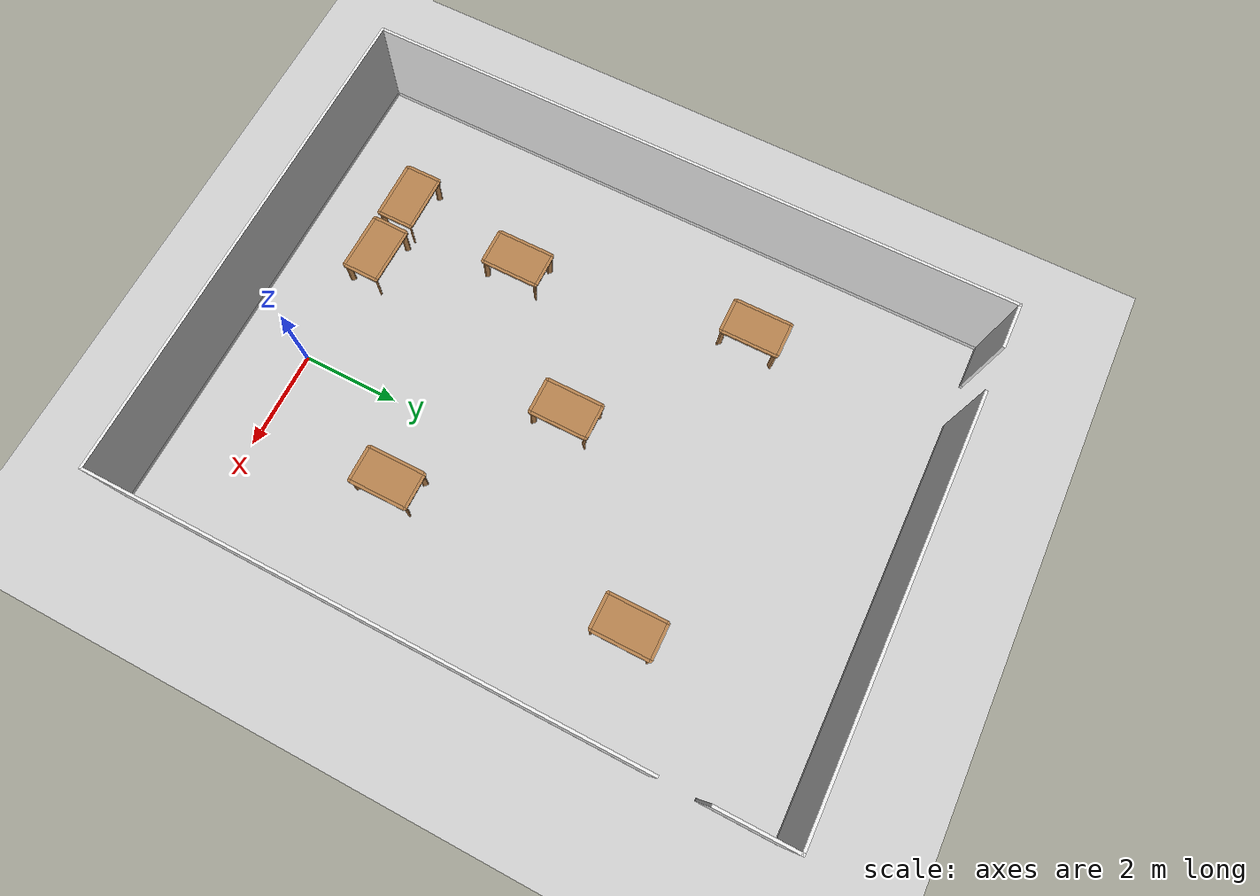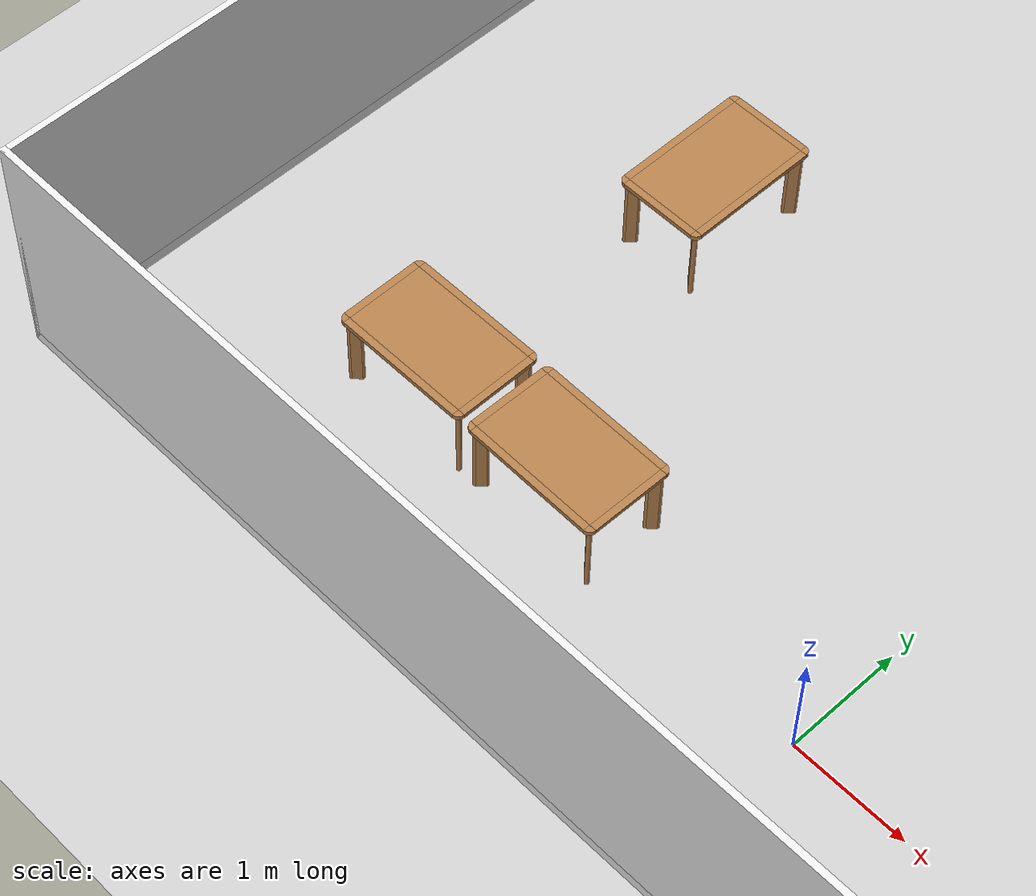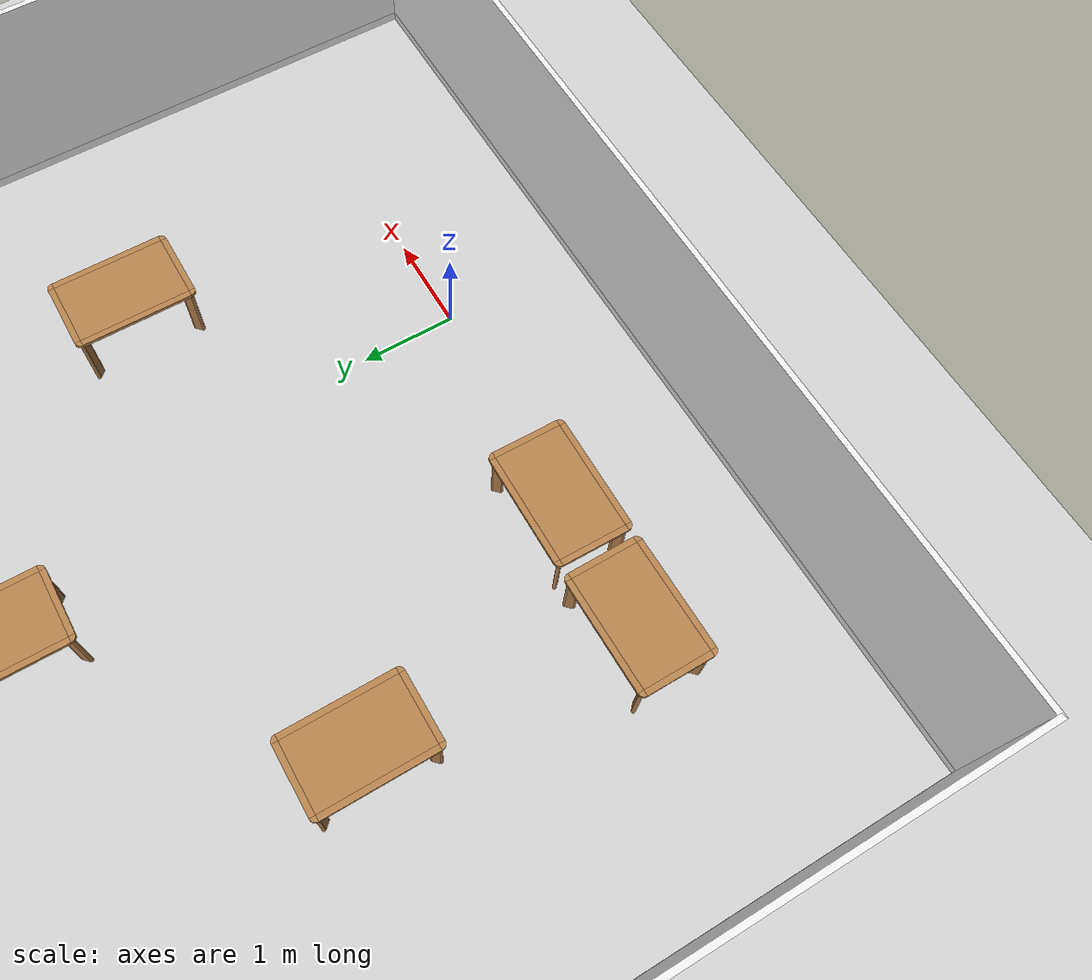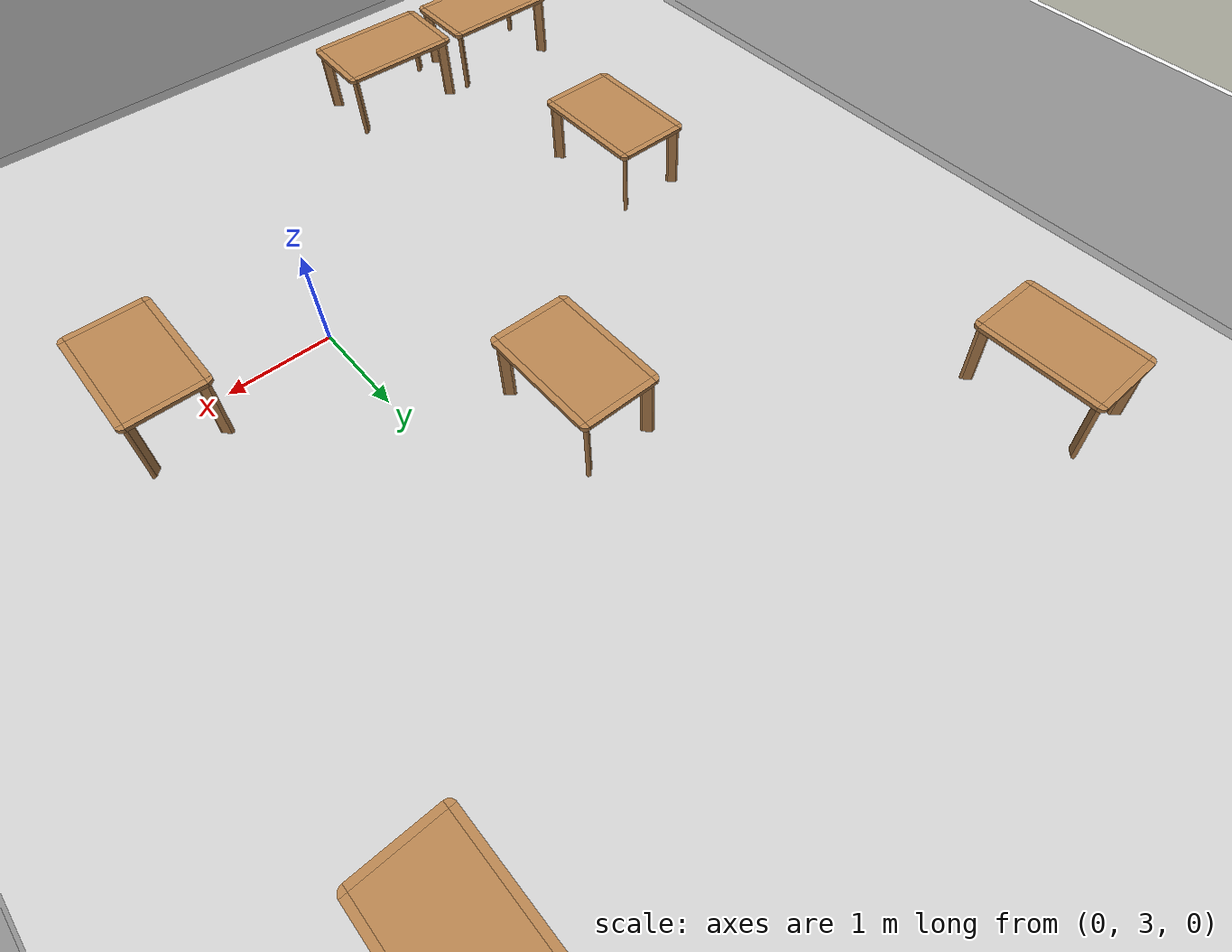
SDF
<sdf version="1.7">
 <world name="default">
  <light name="sun" type="directional">
   <pose>0 0 10 0 -0 0</pose>
   <diffuse>0.8 0.8 0.8 1</diffuse>
   <specular>0.2 0.2 0.2 1</specular>
   <attenuation><range>1000</range><constant>0</constant><linear>0</linear><quadratic>0</quadratic></attenuation>
   <direction>-0.5 0.1 -0.9</direction>
   <spot><inner_angle>0</inner_angle><outer_angle>0</outer_angle><falloff>0</falloff></spot>
  </light>
  <model name="ground_plane">
   <static>1</static>
   <link name="link">
    <collision name="collision">
     <geometry><plane><normal>0 0 1</normal><size>100 100</size></plane></geometry>
     <surface><friction><ode><mu>100</mu><mu2>50</mu2></ode></friction></surface>
    </collision>
    <visual name="visual">
     <cast_shadows>0</cast_shadows>
     <geometry><plane><normal>0 0 1</normal><size>100 100</size></plane></geometry>
     <material>
      <script><uri>file://media/materials/scripts/gazebo.material</uri><name>Gazebo/Grey</name></script>
     </material>
    </visual>
   </link>
  </model>
  <gravity>0 0 -9.8</gravity>
  <magnetic_field>6e-06 2.3e-05 -4.2e-05</magnetic_field>
  <atmosphere type="adiabatic"/>
  <physics type="ode">
   <max_step_size>0.001</max_step_size>
   <real_time_factor>1</real_time_factor>
   <real_time_update_rate>1000</real_time_update_rate>
  </physics>
  <scene><ambient>0.4 0.4 0.4 1</ambient><background>0.7 0.7 0.7 1</background><shadows>1</shadows></scene>
  <spherical_coordinates>
   <surface_model>EARTH_WGS84</surface_model>
   <latitude_deg>0</latitude_deg>
   <longitude_deg>0</longitude_deg>
   <elevation>0</elevation>
   <heading_deg>0</heading_deg>
  </spherical_coordinates>
  <model name="full_outside_wall">
   <link name="link">
    <inertial>
     <mass>50</mass>
     <inertia><ixx>1</ixx><ixy>0</ixy><ixz>0</ixz><iyy>1</iyy><iyz>0</iyz><izz>1</izz></inertia>
    </inertial>
    <visual name="x00_13y00_bottom_frame">
     <pose>5.0375 -0.0275 0.05 0 -0 0</pose>
     <geometry><box><size>10.185 0.055 0.1</size></box></geometry>
     <material>
      <script><uri>model://base_materials/color/scripts</uri><name>hsr_color/white</name></script>
     </material>
    </visual>
    <collision name="x00_13y00_collision_bottom_frame">
     <pose>5.0375 -0.0275 0.05 0 -0 0</pose>
     <geometry><box><size>10.185 0.055 0.1</size></box></geometry>
    </collision>
    <visual name="wall_x00_13y00">
     <pose>5.0375 -0.0275 1.095 0 -0 0</pose>
     <geometry><box><size>10.185 0.055 1.99</size></box></geometry>
     <material>
      <script>
       <uri>model://base_materials/wall/scripts</uri>
       <uri>model://base_materials/wall/textures</uri>
       <name>wall/white_noise</name>
      </script>
     </material>
    </visual>
    <collision name="wall_x00_13y00">
     <pose>5.0375 -0.002 1.095 0 -0 0</pose>
     <geometry><box><size>10.08 0.055 1.99</size></box></geometry>
    </collision>
    <visual name="x00y00_15_bottom_frame">
     <pose>-0.0275 6.59 0.05 0 -0 0</pose>
     <geometry><box><size>0.055 13.29 0.1</size></box></geometry>
     <material>
      <script><uri>model://base_materials/color/scripts</uri><name>hsr_color/white</name></script>
     </material>
    </visual>
    <collision name="x00y00_15_collision_bottom_frame">
     <pose>-0.0275 6.59 0.05 0 -0 0</pose>
     <geometry><box><size>0.055 13.29 0.1</size></box></geometry>
    </collision>
    <visual name="wall_x00y00_15">
     <pose>-0.0275 6.59 1.095 0 -0 0</pose>
     <geometry><box><size>0.055 13.29 1.99</size></box></geometry>
     <material>
      <script>
       <uri>model://base_materials/wall/scripts</uri>
       <uri>model://base_materials/wall/textures</uri>
       <name>wall/white_noise</name>
      </script>
     </material>
    </visual>
    <collision name="wall_x00y00_x00y15">
     <pose>-0.002 6.59 1.095 0 -0 0</pose>
     <geometry><box><size>0.002 13.29 1.99</size></box></geometry>
    </collision>
    <visual name="x13y00_12_bottom_frame">
     <pose>10.1025 5.3725 0.05 0 -0 0</pose>
     <geometry><box><size>0.055 10.855 0.1</size></box></geometry>
     <material>
      <script><uri>model://base_materials/color/scripts</uri><name>hsr_color/white</name></script>
     </material>
    </visual>
    <collision name="x13y00_12_collision_bottom_frame">
     <pose>10.1025 5.3725 0.05 0 -0 0</pose>
     <geometry><box><size>0.055 10.855 0.1</size></box></geometry>
    </collision>
    <visual name="wall_x13y00_12">
     <pose>10.1025 5.3725 1.095 0 -0 0</pose>
     <geometry><box><size>0.055 10.855 1.99</size></box></geometry>
     <material>
      <script>
       <uri>model://base_materials/wall/scripts</uri>
       <uri>model://base_materials/wall/textures</uri>
       <name>wall/white_noise</name>
      </script>
     </material>
    </visual>
    <collision name="wall_x13y00_12">
     <pose>10.1025 5.3725 1.095 0 -0 0</pose>
     <geometry><box><size>0.055 10.855 1.99</size></box></geometry>
    </collision>
    <visual name="x13y14_16_bottom_frame">
     <pose>10.1025 12.4675 0.05 0 -0 0</pose>
     <geometry><box><size>0.055 1.535 0.1</size></box></geometry>
     <material>
      <script><uri>model://base_materials/color/scripts</uri><name>hsr_color/white</name></script>
     </material>
    </visual>
    <collision name="x13y14_16_collision_bottom_frame">
     <pose>10.1025 12.4675 0.05 0 -0 0</pose>
     <geometry><box><size>0.055 1.535 0.1</size></box></geometry>
    </collision>
    <visual name="wall_x13y14_x13y16">
     <pose>10.1025 12.4675 1.095 0 -0 0</pose>
     <geometry><box><size>0.055 1.535 1.99</size></box></geometry>
     <material>
      <script>
       <uri>model://base_materials/wall/scripts</uri>
       <uri>model://base_materials/wall/textures</uri>
       <name>wall/white_noise</name>
      </script>
     </material>
    </visual>
    <collision name="wall_x13y14_x13y16">
     <pose>10.1025 12.4675 1.095 0 -0 0</pose>
     <geometry><box><size>0.055 1.535 1.99</size></box></geometry>
    </collision>
    <visual name="x00_01y16_bottom_frame">
     <pose>0.4225 13.2075 0.05 0 -0 0</pose>
     <geometry><box><size>0.955 0.055 0.1</size></box></geometry>
     <material>
      <script><uri>model://base_materials/color/scripts</uri><name>hsr_color/white</name></script>
     </material>
    </visual>
    <collision name="x00_01y16_collision_bottom_frame">
     <pose>0.4225 13.2075 0.05 0 -0 0</pose>
     <geometry><box><size>0.955 0.055 0.1</size></box></geometry>
    </collision>
    <visual name="wall_x00_01y16">
     <pose>0.4225 13.2075 1.095 0 -0 0</pose>
     <geometry><box><size>0.955 0.055 1.99</size></box></geometry>
     <material>
      <script>
       <uri>model://base_materials/wall/scripts</uri>
       <uri>model://base_materials/wall/textures</uri>
       <name>wall/white_noise</name>
      </script>
     </material>
    </visual>
    <collision name="wall_x00_x01y16">
     <pose>0.4225 13.2075 1.095 0 -0 0</pose>
     <geometry><box><size>0.955 0.055 1.99</size></box></geometry>
    </collision>
    <visual name="x03_13y16_bottom_frame">
     <pose>5.965 13.2075 0.05 0 -0 0</pose>
     <geometry><box><size>8.33 0.05 0.1</size></box></geometry>
     <material>
      <script><uri>model://base_materials/color/scripts</uri><name>hsr_color/white</name></script>
     </material>
    </visual>
    <collision name="x03_13y16_collision_bottom_frame">
     <pose>5.965 13.2075 0.05 0 -0 0</pose>
     <geometry><box><size>8.33 0.05 0.1</size></box></geometry>
    </collision>
    <visual name="wall_x03_13y16">
     <pose>5.965 13.2075 1.095 0 -0 0</pose>
     <geometry><box><size>8.33 0.055 1.99</size></box></geometry>
     <material>
      <script>
       <uri>model://base_materials/wall/scripts</uri>
       <uri>model://base_materials/wall/textures</uri>
       <name>wall/white_noise</name>
      </script>
     </material>
    </visual>
    <collision name="wall_x03_13y16">
     <pose>5.965 13.2075 1.095 0 -0 0</pose>
     <geometry><box><size>8.33 0.055 1.99</size></box></geometry>
    </collision>
    <velocity_decay><linear>0</linear><angular>0</angular></velocity_decay>
   </link>
   <static>1</static>
   <pose>-6.16587 -1.46718 0 0 -0 0</pose>
  </model>
  <model name="kitchen_table">
   <link name="link">
    <inertial>
     <mass>10</mass>
     <inertia><ixx>1</ixx><ixy>0</ixy><ixz>0</ixz><iyy>1</iyy><iyz>0</iyz><izz>1</izz></inertia>
    </inertial>
    <visual name="center_board">
     <pose>0 0 0.68 0 -0 0</pose>
     <geometry><box><size>0.68 1.13 0.04</size></box></geometry>
     <material>
      <script><uri>model://base_materials/wood/scripts/wood.material</uri><name>base_materials/wood</name></script>
     </material>
    </visual>
    <collision name="collision_center_board">
     <pose>0 0 0.68 0 -0 0</pose>
     <geometry><box><size>0.68 1.13 0.04</size></box></geometry>
    </collision>
    <visual name="front_board">
     <pose>0.37 0 0.68 0 -0 0</pose>
     <geometry><box><size>0.06 1.13 0.04</size></box></geometry>
     <material>
      <script><uri>model://base_materials/wood/scripts/wood.material</uri><name>base_materials/wood</name></script>
     </material>
    </visual>
    <collision name="collision_front_board">
     <pose>0.37 0 0.68 0 -0 0</pose>
     <geometry><box><size>0.06 1.13 0.04</size></box></geometry>
    </collision>
    <visual name="back_board">
     <pose>-0.37 0 0.68 0 -0 0</pose>
     <geometry><box><size>0.06 1.13 0.04</size></box></geometry>
     <material>
      <script><uri>model://base_materials/wood/scripts/wood.material</uri><name>base_materials/wood</name></script>
     </material>
    </visual>
    <collision name="collision_back_board">
     <pose>-0.37 0 0.68 0 -0 0</pose>
     <geometry><box><size>0.06 1.13 0.04</size></box></geometry>
    </collision>
    <visual name="right_board">
     <pose>0 0.595 0.68 0 -0 0</pose>
     <geometry><box><size>0.68 0.06 0.04</size></box></geometry>
     <material>
      <script><uri>model://base_materials/wood/scripts/wood.material</uri><name>base_materials/wood</name></script>
     </material>
    </visual>
    <collision name="collision_right_board">
     <pose>0 0.595 0.68 0 -0 0</pose>
     <geometry><box><size>0.68 0.06 0.04</size></box></geometry>
    </collision>
    <visual name="left_board">
     <pose>0 -0.595 0.68 0 -0 0</pose>
     <geometry><box><size>0.68 0.06 0.04</size></box></geometry>
     <material>
      <script><uri>model://base_materials/wood/scripts/wood.material</uri><name>base_materials/wood</name></script>
     </material>
    </visual>
    <collision name="collision_left_board">
     <pose>0 -0.595 0.68 0 -0 0</pose>
     <geometry><box><size>0.68 0.06 0.04</size></box></geometry>
    </collision>
    <visual name="front_right_corner_board">
     <pose>0.34 0.565 0.68 0 -0 0</pose>
     <geometry><cylinder><radius>0.06</radius><length>0.039</length></cylinder></geometry>
     <material>
      <script><uri>model://base_materials/wood/scripts/wood.material</uri><name>base_materials/wood</name></script>
     </material>
    </visual>
    <collision name="collision_front_right_corner_board">
     <pose>0.34 0.565 0.68 0 -0 0</pose>
     <geometry><cylinder><radius>0.06</radius><length>0.039</length></cylinder></geometry>
    </collision>
    <visual name="front_left_corner_board">
     <pose>0.34 -0.565 0.68 0 -0 0</pose>
     <geometry><cylinder><radius>0.06</radius><length>0.039</length></cylinder></geometry>
     <material>
      <script><uri>model://base_materials/wood/scripts/wood.material</uri><name>base_materials/wood</name></script>
     </material>
    </visual>
    <collision name="collision_front_left_corner_board">
     <pose>0.34 -0.565 0.68 0 -0 0</pose>
     <geometry><cylinder><radius>0.06</radius><length>0.039</length></cylinder></geometry>
    </collision>
    <visual name="front_back_right_corner_board">
     <pose>-0.34 0.565 0.68 0 -0 0</pose>
     <geometry><cylinder><radius>0.06</radius><length>0.039</length></cylinder></geometry>
     <material>
      <script><uri>model://base_materials/wood/scripts/wood.material</uri><name>base_materials/wood</name></script>
     </material>
    </visual>
    <collision name="collision_back_right_corner_board">
     <pose>-0.34 0.565 0.68 0 -0 0</pose>
     <geometry><cylinder><radius>0.06</radius><length>0.039</length></cylinder></geometry>
    </collision>
    <visual name="front_back_left_corner_board">
     <pose>-0.34 -0.565 0.68 0 -0 0</pose>
     <geometry><cylinder><radius>0.06</radius><length>0.039</length></cylinder></geometry>
     <material>
      <script><uri>model://base_materials/wood/scripts/wood.material</uri><name>base_materials/wood</name></script>
     </material>
    </visual>
    <collision name="collision_back_left_corner_board">
     <pose>-0.34 -0.565 0.68 0 -0 0</pose>
     <geometry><cylinder><radius>0.06</radius><length>0.039</length></cylinder></geometry>
    </collision>
    <visual name="front_left_corner_frame1">
     <pose>0.345858 -0.57086 0.33 0 -0 0</pose>
     <geometry><cylinder><radius>0.02</radius><length>0.66</length></cylinder></geometry>
     <material>
      <script><uri>model://base_materials/wood/scripts/wood.material</uri><name>base_materials/wood</name></script>
     </material>
    </visual>
    <collision name="collision_front_left_corner_frame1">
     <pose>0.345858 -0.57086 0.33 0 -0 0</pose>
     <geometry><cylinder><radius>0.02</radius><length>0.66</length></cylinder></geometry>
    </collision>
    <visual name="front_left_corner_frame2">
     <pose>0.317574 -0.54257 0.33 0 -0 0.7854</pose>
     <geometry><box><size>0.04 0.08 0.66</size></box></geometry>
     <material>
      <script><uri>model://base_materials/wood/scripts/wood.material</uri><name>base_materials/wood</name></script>
     </material>
    </visual>
    <collision name="collision_front_left_corner_frame2">
     <pose>0.317574 -0.54257 0.33 0 -0 0.7854</pose>
     <geometry><box><size>0.04 0.08 0.66</size></box></geometry>
    </collision>
    <visual name="front_left_corner_frame3">
     <pose>0.289289 -0.51429 0.33 0 -0 0</pose>
     <geometry><cylinder><radius>0.02</radius><length>0.66</length></cylinder></geometry>
     <material>
      <script><uri>model://base_materials/wood/scripts/wood.material</uri><name>base_materials/wood</name></script>
     </material>
    </visual>
    <collision name="collision_front_left_corner_frame3">
     <pose>0.289289 -0.51429 0.33 0 -0 0</pose>
     <geometry><cylinder><radius>0.02</radius><length>0.66</length></cylinder></geometry>
    </collision>
    <visual name="front_right_corner_frame1">
     <pose>0.345858 0.57086 0.33 0 -0 0</pose>
     <geometry><cylinder><radius>0.02</radius><length>0.66</length></cylinder></geometry>
     <material>
      <script><uri>model://base_materials/wood/scripts/wood.material</uri><name>base_materials/wood</name></script>
     </material>
    </visual>
    <collision name="collision_front_right_corner_frame1">
     <pose>0.345858 0.57086 0.33 0 -0 0</pose>
     <geometry><cylinder><radius>0.02</radius><length>0.66</length></cylinder></geometry>
    </collision>
    <visual name="front_right_corner_frame2">
     <pose>0.317574 0.54257 0.33 0 0 -0.7854</pose>
     <geometry><box><size>0.04 0.08 0.66</size></box></geometry>
     <material>
      <script><uri>model://base_materials/wood/scripts/wood.material</uri><name>base_materials/wood</name></script>
     </material>
    </visual>
    <collision name="collision_front_right_corner_frame2">
     <pose>0.317574 0.54257 0.33 0 0 -0.7854</pose>
     <geometry><box><size>0.04 0.08 0.66</size></box></geometry>
    </collision>
    <visual name="front_right_corner_frame3">
     <pose>0.289289 0.51429 0.33 0 -0 0</pose>
     <geometry><cylinder><radius>0.02</radius><length>0.66</length></cylinder></geometry>
     <material>
      <script><uri>model://base_materials/wood/scripts/wood.material</uri><name>base_materials/wood</name></script>
     </material>
    </visual>
    <collision name="collision_front_right_corner_frame3">
     <pose>0.289289 0.51429 0.33 0 -0 0</pose>
     <geometry><cylinder><radius>0.02</radius><length>0.66</length></cylinder></geometry>
    </collision>
    <visual name="back_left_corner_frame1">
     <pose>-0.345858 -0.57086 0.33 0 -0 0</pose>
     <geometry><cylinder><radius>0.02</radius><length>0.66</length></cylinder></geometry>
     <material>
      <script><uri>model://base_materials/wood/scripts/wood.material</uri><name>base_materials/wood</name></script>
     </material>
    </visual>
    <collision name="collision_back_left_corner_frame1">
     <pose>-0.345858 -0.57086 0.33 0 -0 0</pose>
     <geometry><cylinder><radius>0.02</radius><length>0.66</length></cylinder></geometry>
    </collision>
    <visual name="back_left_corner_frame2">
     <pose>-0.317574 -0.54257 0.33 0 0 -0.7854</pose>
     <geometry><box><size>0.04 0.08 0.66</size></box></geometry>
     <material>
      <script><uri>model://base_materials/wood/scripts/wood.material</uri><name>base_materials/wood</name></script>
     </material>
    </visual>
    <collision name="collision_back_left_corner_frame2">
     <pose>-0.317574 -0.54257 0.33 0 0 -0.7854</pose>
     <geometry><box><size>0.04 0.08 0.66</size></box></geometry>
    </collision>
    <visual name="back_left_corner_frame3">
     <pose>-0.289289 -0.51429 0.33 0 -0 0</pose>
     <geometry><cylinder><radius>0.02</radius><length>0.66</length></cylinder></geometry>
     <material>
      <script><uri>model://base_materials/wood/scripts/wood.material</uri><name>base_materials/wood</name></script>
     </material>
    </visual>
    <collision name="collision_back_left_corner_frame3">
     <pose>-0.289289 -0.51429 0.33 0 -0 0</pose>
     <geometry><cylinder><radius>0.02</radius><length>0.66</length></cylinder></geometry>
    </collision>
    <visual name="back_right_corner_frame1">
     <pose>-0.345858 0.57086 0.33 0 -0 0</pose>
     <geometry><cylinder><radius>0.02</radius><length>0.66</length></cylinder></geometry>
     <material>
      <script><uri>model://base_materials/wood/scripts/wood.material</uri><name>base_materials/wood</name></script>
     </material>
    </visual>
    <collision name="collision_back_right_corner_frame1">
     <pose>-0.345858 0.57086 0.33 0 -0 0</pose>
     <geometry><cylinder><radius>0.02</radius><length>0.66</length></cylinder></geometry>
    </collision>
    <visual name="back_right_corner_frame2">
     <pose>-0.317574 0.54257 0.33 0 -0 0.7854</pose>
     <geometry><box><size>0.04 0.08 0.66</size></box></geometry>
     <material>
      <script><uri>model://base_materials/wood/scripts/wood.material</uri><name>base_materials/wood</name></script>
     </material>
    </visual>
    <collision name="collision_back_right_corner_frame2">
     <pose>-0.317574 0.54257 0.33 0 -0 0.7854</pose>
     <geometry><box><size>0.04 0.08 0.66</size></box></geometry>
    </collision>
    <visual name="back_right_corner_frame3">
     <pose>-0.289289 0.51429 0.33 0 -0 0</pose>
     <geometry><cylinder><radius>0.02</radius><length>0.66</length></cylinder></geometry>
     <material>
      <script><uri>model://base_materials/wood/scripts/wood.material</uri><name>base_materials/wood</name></script>
     </material>
    </visual>
    <collision name="collision_back_right_corner_frame3">
     <pose>-0.289289 0.51429 0.33 0 -0 0</pose>
     <geometry><cylinder><radius>0.02</radius><length>0.66</length></cylinder></geometry>
    </collision>
    <velocity_decay><linear>0</linear><angular>0</angular></velocity_decay>
   </link>
   <static>0</static>
   <pose>-1.16726 5.15853 -2e-06 0 -7e-06 0</pose>
  </model>
  <model name="kitchen_table_clone">
   <link name="link">
    <inertial>
     <mass>10</mass>
     <inertia><ixx>1</ixx><ixy>0</ixy><ixz>0</ixz><iyy>1</iyy><iyz>0</iyz><izz>1</izz></inertia>
    </inertial>
    <visual name="center_board">
     <pose>0 0 0.68 0 -0 0</pose>
     <geometry><box><size>0.68 1.13 0.04</size></box></geometry>
     <material>
      <script><uri>model://base_materials/wood/scripts/wood.material</uri><name>base_materials/wood</name></script>
     </material>
    </visual>
    <collision name="collision_center_board">
     <pose>0 0 0.68 0 -0 0</pose>
     <geometry><box><size>0.68 1.13 0.04</size></box></geometry>
    </collision>
    <visual name="front_board">
     <pose>0.37 0 0.68 0 -0 0</pose>
     <geometry><box><size>0.06 1.13 0.04</size></box></geometry>
     <material>
      <script><uri>model://base_materials/wood/scripts/wood.material</uri><name>base_materials/wood</name></script>
     </material>
    </visual>
    <collision name="collision_front_board">
     <pose>0.37 0 0.68 0 -0 0</pose>
     <geometry><box><size>0.06 1.13 0.04</size></box></geometry>
    </collision>
    <visual name="back_board">
     <pose>-0.37 0 0.68 0 -0 0</pose>
     <geometry><box><size>0.06 1.13 0.04</size></box></geometry>
     <material>
      <script><uri>model://base_materials/wood/scripts/wood.material</uri><name>base_materials/wood</name></script>
     </material>
    </visual>
    <collision name="collision_back_board">
     <pose>-0.37 0 0.68 0 -0 0</pose>
     <geometry><box><size>0.06 1.13 0.04</size></box></geometry>
    </collision>
    <visual name="right_board">
     <pose>0 0.595 0.68 0 -0 0</pose>
     <geometry><box><size>0.68 0.06 0.04</size></box></geometry>
     <material>
      <script><uri>model://base_materials/wood/scripts/wood.material</uri><name>base_materials/wood</name></script>
     </material>
    </visual>
    <collision name="collision_right_board">
     <pose>0 0.595 0.68 0 -0 0</pose>
     <geometry><box><size>0.68 0.06 0.04</size></box></geometry>
    </collision>
    <visual name="left_board">
     <pose>0 -0.595 0.68 0 -0 0</pose>
     <geometry><box><size>0.68 0.06 0.04</size></box></geometry>
     <material>
      <script><uri>model://base_materials/wood/scripts/wood.material</uri><name>base_materials/wood</name></script>
     </material>
    </visual>
    <collision name="collision_left_board">
     <pose>0 -0.595 0.68 0 -0 0</pose>
     <geometry><box><size>0.68 0.06 0.04</size></box></geometry>
    </collision>
    <visual name="front_right_corner_board">
     <pose>0.34 0.565 0.68 0 -0 0</pose>
     <geometry><cylinder><radius>0.06</radius><length>0.039</length></cylinder></geometry>
     <material>
      <script><uri>model://base_materials/wood/scripts/wood.material</uri><name>base_materials/wood</name></script>
     </material>
    </visual>
    <collision name="collision_front_right_corner_board">
     <pose>0.34 0.565 0.68 0 -0 0</pose>
     <geometry><cylinder><radius>0.06</radius><length>0.039</length></cylinder></geometry>
    </collision>
    <visual name="front_left_corner_board">
     <pose>0.34 -0.565 0.68 0 -0 0</pose>
     <geometry><cylinder><radius>0.06</radius><length>0.039</length></cylinder></geometry>
     <material>
      <script><uri>model://base_materials/wood/scripts/wood.material</uri><name>base_materials/wood</name></script>
     </material>
    </visual>
    <collision name="collision_front_left_corner_board">
     <pose>0.34 -0.565 0.68 0 -0 0</pose>
     <geometry><cylinder><radius>0.06</radius><length>0.039</length></cylinder></geometry>
    </collision>
    <visual name="front_back_right_corner_board">
     <pose>-0.34 0.565 0.68 0 -0 0</pose>
     <geometry><cylinder><radius>0.06</radius><length>0.039</length></cylinder></geometry>
     <material>
      <script><uri>model://base_materials/wood/scripts/wood.material</uri><name>base_materials/wood</name></script>
     </material>
    </visual>
    <collision name="collision_back_right_corner_board">
     <pose>-0.34 0.565 0.68 0 -0 0</pose>
     <geometry><cylinder><radius>0.06</radius><length>0.039</length></cylinder></geometry>
    </collision>
    <visual name="front_back_left_corner_board">
     <pose>-0.34 -0.565 0.68 0 -0 0</pose>
     <geometry><cylinder><radius>0.06</radius><length>0.039</length></cylinder></geometry>
     <material>
      <script><uri>model://base_materials/wood/scripts/wood.material</uri><name>base_materials/wood</name></script>
     </material>
    </visual>
    <collision name="collision_back_left_corner_board">
     <pose>-0.34 -0.565 0.68 0 -0 0</pose>
     <geometry><cylinder><radius>0.06</radius><length>0.039</length></cylinder></geometry>
    </collision>
    <visual name="front_left_corner_frame1">
     <pose>0.345858 -0.57086 0.33 0 -0 0</pose>
     <geometry><cylinder><radius>0.02</radius><length>0.66</length></cylinder></geometry>
     <material>
      <script><uri>model://base_materials/wood/scripts/wood.material</uri><name>base_materials/wood</name></script>
     </material>
    </visual>
    <collision name="collision_front_left_corner_frame1">
     <pose>0.345858 -0.57086 0.33 0 -0 0</pose>
     <geometry><cylinder><radius>0.02</radius><length>0.66</length></cylinder></geometry>
    </collision>
    <visual name="front_left_corner_frame2">
     <pose>0.317574 -0.54257 0.33 0 -0 0.7854</pose>
     <geometry><box><size>0.04 0.08 0.66</size></box></geometry>
     <material>
      <script><uri>model://base_materials/wood/scripts/wood.material</uri><name>base_materials/wood</name></script>
     </material>
    </visual>
    <collision name="collision_front_left_corner_frame2">
     <pose>0.317574 -0.54257 0.33 0 -0 0.7854</pose>
     <geometry><box><size>0.04 0.08 0.66</size></box></geometry>
    </collision>
    <visual name="front_left_corner_frame3">
     <pose>0.289289 -0.51429 0.33 0 -0 0</pose>
     <geometry><cylinder><radius>0.02</radius><length>0.66</length></cylinder></geometry>
     <material>
      <script><uri>model://base_materials/wood/scripts/wood.material</uri><name>base_materials/wood</name></script>
     </material>
    </visual>
    <collision name="collision_front_left_corner_frame3">
     <pose>0.289289 -0.51429 0.33 0 -0 0</pose>
     <geometry><cylinder><radius>0.02</radius><length>0.66</length></cylinder></geometry>
    </collision>
    <visual name="front_right_corner_frame1">
     <pose>0.345858 0.57086 0.33 0 -0 0</pose>
     <geometry><cylinder><radius>0.02</radius><length>0.66</length></cylinder></geometry>
     <material>
      <script><uri>model://base_materials/wood/scripts/wood.material</uri><name>base_materials/wood</name></script>
     </material>
    </visual>
    <collision name="collision_front_right_corner_frame1">
     <pose>0.345858 0.57086 0.33 0 -0 0</pose>
     <geometry><cylinder><radius>0.02</radius><length>0.66</length></cylinder></geometry>
    </collision>
    <visual name="front_right_corner_frame2">
     <pose>0.317574 0.54257 0.33 0 0 -0.7854</pose>
     <geometry><box><size>0.04 0.08 0.66</size></box></geometry>
     <material>
      <script><uri>model://base_materials/wood/scripts/wood.material</uri><name>base_materials/wood</name></script>
     </material>
    </visual>
    <collision name="collision_front_right_corner_frame2">
     <pose>0.317574 0.54257 0.33 0 0 -0.7854</pose>
     <geometry><box><size>0.04 0.08 0.66</size></box></geometry>
    </collision>
    <visual name="front_right_corner_frame3">
     <pose>0.289289 0.51429 0.33 0 -0 0</pose>
     <geometry><cylinder><radius>0.02</radius><length>0.66</length></cylinder></geometry>
     <material>
      <script><uri>model://base_materials/wood/scripts/wood.material</uri><name>base_materials/wood</name></script>
     </material>
    </visual>
    <collision name="collision_front_right_corner_frame3">
     <pose>0.289289 0.51429 0.33 0 -0 0</pose>
     <geometry><cylinder><radius>0.02</radius><length>0.66</length></cylinder></geometry>
    </collision>
    <visual name="back_left_corner_frame1">
     <pose>-0.345858 -0.57086 0.33 0 -0 0</pose>
     <geometry><cylinder><radius>0.02</radius><length>0.66</length></cylinder></geometry>
     <material>
      <script><uri>model://base_materials/wood/scripts/wood.material</uri><name>base_materials/wood</name></script>
     </material>
    </visual>
    <collision name="collision_back_left_corner_frame1">
     <pose>-0.345858 -0.57086 0.33 0 -0 0</pose>
     <geometry><cylinder><radius>0.02</radius><length>0.66</length></cylinder></geometry>
    </collision>
    <visual name="back_left_corner_frame2">
     <pose>-0.317574 -0.54257 0.33 0 0 -0.7854</pose>
     <geometry><box><size>0.04 0.08 0.66</size></box></geometry>
     <material>
      <script><uri>model://base_materials/wood/scripts/wood.material</uri><name>base_materials/wood</name></script>
     </material>
    </visual>
    <collision name="collision_back_left_corner_frame2">
     <pose>-0.317574 -0.54257 0.33 0 0 -0.7854</pose>
     <geometry><box><size>0.04 0.08 0.66</size></box></geometry>
    </collision>
    <visual name="back_left_corner_frame3">
     <pose>-0.289289 -0.51429 0.33 0 -0 0</pose>
     <geometry><cylinder><radius>0.02</radius><length>0.66</length></cylinder></geometry>
     <material>
      <script><uri>model://base_materials/wood/scripts/wood.material</uri><name>base_materials/wood</name></script>
     </material>
    </visual>
    <collision name="collision_back_left_corner_frame3">
     <pose>-0.289289 -0.51429 0.33 0 -0 0</pose>
     <geometry><cylinder><radius>0.02</radius><length>0.66</length></cylinder></geometry>
    </collision>
    <visual name="back_right_corner_frame1">
     <pose>-0.345858 0.57086 0.33 0 -0 0</pose>
     <geometry><cylinder><radius>0.02</radius><length>0.66</length></cylinder></geometry>
     <material>
      <script><uri>model://base_materials/wood/scripts/wood.material</uri><name>base_materials/wood</name></script>
     </material>
    </visual>
    <collision name="collision_back_right_corner_frame1">
     <pose>-0.345858 0.57086 0.33 0 -0 0</pose>
     <geometry><cylinder><radius>0.02</radius><length>0.66</length></cylinder></geometry>
    </collision>
    <visual name="back_right_corner_frame2">
     <pose>-0.317574 0.54257 0.33 0 -0 0.7854</pose>
     <geometry><box><size>0.04 0.08 0.66</size></box></geometry>
     <material>
      <script><uri>model://base_materials/wood/scripts/wood.material</uri><name>base_materials/wood</name></script>
     </material>
    </visual>
    <collision name="collision_back_right_corner_frame2">
     <pose>-0.317574 0.54257 0.33 0 -0 0.7854</pose>
     <geometry><box><size>0.04 0.08 0.66</size></box></geometry>
    </collision>
    <visual name="back_right_corner_frame3">
     <pose>-0.289289 0.51429 0.33 0 -0 0</pose>
     <geometry><cylinder><radius>0.02</radius><length>0.66</length></cylinder></geometry>
     <material>
      <script><uri>model://base_materials/wood/scripts/wood.material</uri><name>base_materials/wood</name></script>
     </material>
    </visual>
    <collision name="collision_back_right_corner_frame3">
     <pose>-0.289289 0.51429 0.33 0 -0 0</pose>
     <geometry><cylinder><radius>0.02</radius><length>0.66</length></cylinder></geometry>
    </collision>
    <velocity_decay><linear>0</linear><angular>0</angular></velocity_decay>
   </link>
   <static>0</static>
   <pose>-2.44109 0.264228 -2e-06 0 -7e-06 -1.58411</pose>
  </model>
  <model name="kitchen_table_clone_0">
   <link name="link">
    <inertial>
     <mass>10</mass>
     <inertia><ixx>1</ixx><ixy>0</ixy><ixz>0</ixz><iyy>1</iyy><iyz>0</iyz><izz>1</izz></inertia>
    </inertial>
    <visual name="center_board">
     <pose>0 0 0.68 0 -0 0</pose>
     <geometry><box><size>0.68 1.13 0.04</size></box></geometry>
     <material>
      <script><uri>model://base_materials/wood/scripts/wood.material</uri><name>base_materials/wood</name></script>
     </material>
    </visual>
    <collision name="collision_center_board">
     <pose>0 0 0.68 0 -0 0</pose>
     <geometry><box><size>0.68 1.13 0.04</size></box></geometry>
    </collision>
    <visual name="front_board">
     <pose>0.37 0 0.68 0 -0 0</pose>
     <geometry><box><size>0.06 1.13 0.04</size></box></geometry>
     <material>
      <script><uri>model://base_materials/wood/scripts/wood.material</uri><name>base_materials/wood</name></script>
     </material>
    </visual>
    <collision name="collision_front_board">
     <pose>0.37 0 0.68 0 -0 0</pose>
     <geometry><box><size>0.06 1.13 0.04</size></box></geometry>
    </collision>
    <visual name="back_board">
     <pose>-0.37 0 0.68 0 -0 0</pose>
     <geometry><box><size>0.06 1.13 0.04</size></box></geometry>
     <material>
      <script><uri>model://base_materials/wood/scripts/wood.material</uri><name>base_materials/wood</name></script>
     </material>
    </visual>
    <collision name="collision_back_board">
     <pose>-0.37 0 0.68 0 -0 0</pose>
     <geometry><box><size>0.06 1.13 0.04</size></box></geometry>
    </collision>
    <visual name="right_board">
     <pose>0 0.595 0.68 0 -0 0</pose>
     <geometry><box><size>0.68 0.06 0.04</size></box></geometry>
     <material>
      <script><uri>model://base_materials/wood/scripts/wood.material</uri><name>base_materials/wood</name></script>
     </material>
    </visual>
    <collision name="collision_right_board">
     <pose>0 0.595 0.68 0 -0 0</pose>
     <geometry><box><size>0.68 0.06 0.04</size></box></geometry>
    </collision>
    <visual name="left_board">
     <pose>0 -0.595 0.68 0 -0 0</pose>
     <geometry><box><size>0.68 0.06 0.04</size></box></geometry>
     <material>
      <script><uri>model://base_materials/wood/scripts/wood.material</uri><name>base_materials/wood</name></script>
     </material>
    </visual>
    <collision name="collision_left_board">
     <pose>0 -0.595 0.68 0 -0 0</pose>
     <geometry><box><size>0.68 0.06 0.04</size></box></geometry>
    </collision>
    <visual name="front_right_corner_board">
     <pose>0.34 0.565 0.68 0 -0 0</pose>
     <geometry><cylinder><radius>0.06</radius><length>0.039</length></cylinder></geometry>
     <material>
      <script><uri>model://base_materials/wood/scripts/wood.material</uri><name>base_materials/wood</name></script>
     </material>
    </visual>
    <collision name="collision_front_right_corner_board">
     <pose>0.34 0.565 0.68 0 -0 0</pose>
     <geometry><cylinder><radius>0.06</radius><length>0.039</length></cylinder></geometry>
    </collision>
    <visual name="front_left_corner_board">
     <pose>0.34 -0.565 0.68 0 -0 0</pose>
     <geometry><cylinder><radius>0.06</radius><length>0.039</length></cylinder></geometry>
     <material>
      <script><uri>model://base_materials/wood/scripts/wood.material</uri><name>base_materials/wood</name></script>
     </material>
    </visual>
    <collision name="collision_front_left_corner_board">
     <pose>0.34 -0.565 0.68 0 -0 0</pose>
     <geometry><cylinder><radius>0.06</radius><length>0.039</length></cylinder></geometry>
    </collision>
    <visual name="front_back_right_corner_board">
     <pose>-0.34 0.565 0.68 0 -0 0</pose>
     <geometry><cylinder><radius>0.06</radius><length>0.039</length></cylinder></geometry>
     <material>
      <script><uri>model://base_materials/wood/scripts/wood.material</uri><name>base_materials/wood</name></script>
     </material>
    </visual>
    <collision name="collision_back_right_corner_board">
     <pose>-0.34 0.565 0.68 0 -0 0</pose>
     <geometry><cylinder><radius>0.06</radius><length>0.039</length></cylinder></geometry>
    </collision>
    <visual name="front_back_left_corner_board">
     <pose>-0.34 -0.565 0.68 0 -0 0</pose>
     <geometry><cylinder><radius>0.06</radius><length>0.039</length></cylinder></geometry>
     <material>
      <script><uri>model://base_materials/wood/scripts/wood.material</uri><name>base_materials/wood</name></script>
     </material>
    </visual>
    <collision name="collision_back_left_corner_board">
     <pose>-0.34 -0.565 0.68 0 -0 0</pose>
     <geometry><cylinder><radius>0.06</radius><length>0.039</length></cylinder></geometry>
    </collision>
    <visual name="front_left_corner_frame1">
     <pose>0.345858 -0.57086 0.33 0 -0 0</pose>
     <geometry><cylinder><radius>0.02</radius><length>0.66</length></cylinder></geometry>
     <material>
      <script><uri>model://base_materials/wood/scripts/wood.material</uri><name>base_materials/wood</name></script>
     </material>
    </visual>
    <collision name="collision_front_left_corner_frame1">
     <pose>0.345858 -0.57086 0.33 0 -0 0</pose>
     <geometry><cylinder><radius>0.02</radius><length>0.66</length></cylinder></geometry>
    </collision>
    <visual name="front_left_corner_frame2">
     <pose>0.317574 -0.54257 0.33 0 -0 0.7854</pose>
     <geometry><box><size>0.04 0.08 0.66</size></box></geometry>
     <material>
      <script><uri>model://base_materials/wood/scripts/wood.material</uri><name>base_materials/wood</name></script>
     </material>
    </visual>
    <collision name="collision_front_left_corner_frame2">
     <pose>0.317574 -0.54257 0.33 0 -0 0.7854</pose>
     <geometry><box><size>0.04 0.08 0.66</size></box></geometry>
    </collision>
    <visual name="front_left_corner_frame3">
     <pose>0.289289 -0.51429 0.33 0 -0 0</pose>
     <geometry><cylinder><radius>0.02</radius><length>0.66</length></cylinder></geometry>
     <material>
      <script><uri>model://base_materials/wood/scripts/wood.material</uri><name>base_materials/wood</name></script>
     </material>
    </visual>
    <collision name="collision_front_left_corner_frame3">
     <pose>0.289289 -0.51429 0.33 0 -0 0</pose>
     <geometry><cylinder><radius>0.02</radius><length>0.66</length></cylinder></geometry>
    </collision>
    <visual name="front_right_corner_frame1">
     <pose>0.345858 0.57086 0.33 0 -0 0</pose>
     <geometry><cylinder><radius>0.02</radius><length>0.66</length></cylinder></geometry>
     <material>
      <script><uri>model://base_materials/wood/scripts/wood.material</uri><name>base_materials/wood</name></script>
     </material>
    </visual>
    <collision name="collision_front_right_corner_frame1">
     <pose>0.345858 0.57086 0.33 0 -0 0</pose>
     <geometry><cylinder><radius>0.02</radius><length>0.66</length></cylinder></geometry>
    </collision>
    <visual name="front_right_corner_frame2">
     <pose>0.317574 0.54257 0.33 0 0 -0.7854</pose>
     <geometry><box><size>0.04 0.08 0.66</size></box></geometry>
     <material>
      <script><uri>model://base_materials/wood/scripts/wood.material</uri><name>base_materials/wood</name></script>
     </material>
    </visual>
    <collision name="collision_front_right_corner_frame2">
     <pose>0.317574 0.54257 0.33 0 0 -0.7854</pose>
     <geometry><box><size>0.04 0.08 0.66</size></box></geometry>
    </collision>
    <visual name="front_right_corner_frame3">
     <pose>0.289289 0.51429 0.33 0 -0 0</pose>
     <geometry><cylinder><radius>0.02</radius><length>0.66</length></cylinder></geometry>
     <material>
      <script><uri>model://base_materials/wood/scripts/wood.material</uri><name>base_materials/wood</name></script>
     </material>
    </visual>
    <collision name="collision_front_right_corner_frame3">
     <pose>0.289289 0.51429 0.33 0 -0 0</pose>
     <geometry><cylinder><radius>0.02</radius><length>0.66</length></cylinder></geometry>
    </collision>
    <visual name="back_left_corner_frame1">
     <pose>-0.345858 -0.57086 0.33 0 -0 0</pose>
     <geometry><cylinder><radius>0.02</radius><length>0.66</length></cylinder></geometry>
     <material>
      <script><uri>model://base_materials/wood/scripts/wood.material</uri><name>base_materials/wood</name></script>
     </material>
    </visual>
    <collision name="collision_back_left_corner_frame1">
     <pose>-0.345858 -0.57086 0.33 0 -0 0</pose>
     <geometry><cylinder><radius>0.02</radius><length>0.66</length></cylinder></geometry>
    </collision>
    <visual name="back_left_corner_frame2">
     <pose>-0.317574 -0.54257 0.33 0 0 -0.7854</pose>
     <geometry><box><size>0.04 0.08 0.66</size></box></geometry>
     <material>
      <script><uri>model://base_materials/wood/scripts/wood.material</uri><name>base_materials/wood</name></script>
     </material>
    </visual>
    <collision name="collision_back_left_corner_frame2">
     <pose>-0.317574 -0.54257 0.33 0 0 -0.7854</pose>
     <geometry><box><size>0.04 0.08 0.66</size></box></geometry>
    </collision>
    <visual name="back_left_corner_frame3">
     <pose>-0.289289 -0.51429 0.33 0 -0 0</pose>
     <geometry><cylinder><radius>0.02</radius><length>0.66</length></cylinder></geometry>
     <material>
      <script><uri>model://base_materials/wood/scripts/wood.material</uri><name>base_materials/wood</name></script>
     </material>
    </visual>
    <collision name="collision_back_left_corner_frame3">
     <pose>-0.289289 -0.51429 0.33 0 -0 0</pose>
     <geometry><cylinder><radius>0.02</radius><length>0.66</length></cylinder></geometry>
    </collision>
    <visual name="back_right_corner_frame1">
     <pose>-0.345858 0.57086 0.33 0 -0 0</pose>
     <geometry><cylinder><radius>0.02</radius><length>0.66</length></cylinder></geometry>
     <material>
      <script><uri>model://base_materials/wood/scripts/wood.material</uri><name>base_materials/wood</name></script>
     </material>
    </visual>
    <collision name="collision_back_right_corner_frame1">
     <pose>-0.345858 0.57086 0.33 0 -0 0</pose>
     <geometry><cylinder><radius>0.02</radius><length>0.66</length></cylinder></geometry>
    </collision>
    <visual name="back_right_corner_frame2">
     <pose>-0.317574 0.54257 0.33 0 -0 0.7854</pose>
     <geometry><box><size>0.04 0.08 0.66</size></box></geometry>
     <material>
      <script><uri>model://base_materials/wood/scripts/wood.material</uri><name>base_materials/wood</name></script>
     </material>
    </visual>
    <collision name="collision_back_right_corner_frame2">
     <pose>-0.317574 0.54257 0.33 0 -0 0.7854</pose>
     <geometry><box><size>0.04 0.08 0.66</size></box></geometry>
    </collision>
    <visual name="back_right_corner_frame3">
     <pose>-0.289289 0.51429 0.33 0 -0 0</pose>
     <geometry><cylinder><radius>0.02</radius><length>0.66</length></cylinder></geometry>
     <material>
      <script><uri>model://base_materials/wood/scripts/wood.material</uri><name>base_materials/wood</name></script>
     </material>
    </visual>
    <collision name="collision_back_right_corner_frame3">
     <pose>-0.289289 0.51429 0.33 0 -0 0</pose>
     <geometry><cylinder><radius>0.02</radius><length>0.66</length></cylinder></geometry>
    </collision>
    <velocity_decay><linear>0</linear><angular>0</angular></velocity_decay>
   </link>
   <static>0</static>
   <pose>1.91253 7.95238 -2e-06 0 -7e-06 0</pose>
  </model>
  <model name="kitchen_table_clone_1">
   <link name="link">
    <inertial>
     <mass>10</mass>
     <inertia><ixx>1</ixx><ixy>0</ixy><ixz>0</ixz><iyy>1</iyy><iyz>0</iyz><izz>1</izz></inertia>
    </inertial>
    <visual name="center_board">
     <pose>0 0 0.68 0 -0 0</pose>
     <geometry><box><size>0.68 1.13 0.04</size></box></geometry>
     <material>
      <script><uri>model://base_materials/wood/scripts/wood.material</uri><name>base_materials/wood</name></script>
     </material>
    </visual>
    <collision name="collision_center_board">
     <pose>0 0 0.68 0 -0 0</pose>
     <geometry><box><size>0.68 1.13 0.04</size></box></geometry>
    </collision>
    <visual name="front_board">
     <pose>0.37 0 0.68 0 -0 0</pose>
     <geometry><box><size>0.06 1.13 0.04</size></box></geometry>
     <material>
      <script><uri>model://base_materials/wood/scripts/wood.material</uri><name>base_materials/wood</name></script>
     </material>
    </visual>
    <collision name="collision_front_board">
     <pose>0.37 0 0.68 0 -0 0</pose>
     <geometry><box><size>0.06 1.13 0.04</size></box></geometry>
    </collision>
    <visual name="back_board">
     <pose>-0.37 0 0.68 0 -0 0</pose>
     <geometry><box><size>0.06 1.13 0.04</size></box></geometry>
     <material>
      <script><uri>model://base_materials/wood/scripts/wood.material</uri><name>base_materials/wood</name></script>
     </material>
    </visual>
    <collision name="collision_back_board">
     <pose>-0.37 0 0.68 0 -0 0</pose>
     <geometry><box><size>0.06 1.13 0.04</size></box></geometry>
    </collision>
    <visual name="right_board">
     <pose>0 0.595 0.68 0 -0 0</pose>
     <geometry><box><size>0.68 0.06 0.04</size></box></geometry>
     <material>
      <script><uri>model://base_materials/wood/scripts/wood.material</uri><name>base_materials/wood</name></script>
     </material>
    </visual>
    <collision name="collision_right_board">
     <pose>0 0.595 0.68 0 -0 0</pose>
     <geometry><box><size>0.68 0.06 0.04</size></box></geometry>
    </collision>
    <visual name="left_board">
     <pose>0 -0.595 0.68 0 -0 0</pose>
     <geometry><box><size>0.68 0.06 0.04</size></box></geometry>
     <material>
      <script><uri>model://base_materials/wood/scripts/wood.material</uri><name>base_materials/wood</name></script>
     </material>
    </visual>
    <collision name="collision_left_board">
     <pose>0 -0.595 0.68 0 -0 0</pose>
     <geometry><box><size>0.68 0.06 0.04</size></box></geometry>
    </collision>
    <visual name="front_right_corner_board">
     <pose>0.34 0.565 0.68 0 -0 0</pose>
     <geometry><cylinder><radius>0.06</radius><length>0.039</length></cylinder></geometry>
     <material>
      <script><uri>model://base_materials/wood/scripts/wood.material</uri><name>base_materials/wood</name></script>
     </material>
    </visual>
    <collision name="collision_front_right_corner_board">
     <pose>0.34 0.565 0.68 0 -0 0</pose>
     <geometry><cylinder><radius>0.06</radius><length>0.039</length></cylinder></geometry>
    </collision>
    <visual name="front_left_corner_board">
     <pose>0.34 -0.565 0.68 0 -0 0</pose>
     <geometry><cylinder><radius>0.06</radius><length>0.039</length></cylinder></geometry>
     <material>
      <script><uri>model://base_materials/wood/scripts/wood.material</uri><name>base_materials/wood</name></script>
     </material>
    </visual>
    <collision name="collision_front_left_corner_board">
     <pose>0.34 -0.565 0.68 0 -0 0</pose>
     <geometry><cylinder><radius>0.06</radius><length>0.039</length></cylinder></geometry>
    </collision>
    <visual name="front_back_right_corner_board">
     <pose>-0.34 0.565 0.68 0 -0 0</pose>
     <geometry><cylinder><radius>0.06</radius><length>0.039</length></cylinder></geometry>
     <material>
      <script><uri>model://base_materials/wood/scripts/wood.material</uri><name>base_materials/wood</name></script>
     </material>
    </visual>
    <collision name="collision_back_right_corner_board">
     <pose>-0.34 0.565 0.68 0 -0 0</pose>
     <geometry><cylinder><radius>0.06</radius><length>0.039</length></cylinder></geometry>
    </collision>
    <visual name="front_back_left_corner_board">
     <pose>-0.34 -0.565 0.68 0 -0 0</pose>
     <geometry><cylinder><radius>0.06</radius><length>0.039</length></cylinder></geometry>
     <material>
      <script><uri>model://base_materials/wood/scripts/wood.material</uri><name>base_materials/wood</name></script>
     </material>
    </visual>
    <collision name="collision_back_left_corner_board">
     <pose>-0.34 -0.565 0.68 0 -0 0</pose>
     <geometry><cylinder><radius>0.06</radius><length>0.039</length></cylinder></geometry>
    </collision>
    <visual name="front_left_corner_frame1">
     <pose>0.345858 -0.57086 0.33 0 -0 0</pose>
     <geometry><cylinder><radius>0.02</radius><length>0.66</length></cylinder></geometry>
     <material>
      <script><uri>model://base_materials/wood/scripts/wood.material</uri><name>base_materials/wood</name></script>
     </material>
    </visual>
    <collision name="collision_front_left_corner_frame1">
     <pose>0.345858 -0.57086 0.33 0 -0 0</pose>
     <geometry><cylinder><radius>0.02</radius><length>0.66</length></cylinder></geometry>
    </collision>
    <visual name="front_left_corner_frame2">
     <pose>0.317574 -0.54257 0.33 0 -0 0.7854</pose>
     <geometry><box><size>0.04 0.08 0.66</size></box></geometry>
     <material>
      <script><uri>model://base_materials/wood/scripts/wood.material</uri><name>base_materials/wood</name></script>
     </material>
    </visual>
    <collision name="collision_front_left_corner_frame2">
     <pose>0.317574 -0.54257 0.33 0 -0 0.7854</pose>
     <geometry><box><size>0.04 0.08 0.66</size></box></geometry>
    </collision>
    <visual name="front_left_corner_frame3">
     <pose>0.289289 -0.51429 0.33 0 -0 0</pose>
     <geometry><cylinder><radius>0.02</radius><length>0.66</length></cylinder></geometry>
     <material>
      <script><uri>model://base_materials/wood/scripts/wood.material</uri><name>base_materials/wood</name></script>
     </material>
    </visual>
    <collision name="collision_front_left_corner_frame3">
     <pose>0.289289 -0.51429 0.33 0 -0 0</pose>
     <geometry><cylinder><radius>0.02</radius><length>0.66</length></cylinder></geometry>
    </collision>
    <visual name="front_right_corner_frame1">
     <pose>0.345858 0.57086 0.33 0 -0 0</pose>
     <geometry><cylinder><radius>0.02</radius><length>0.66</length></cylinder></geometry>
     <material>
      <script><uri>model://base_materials/wood/scripts/wood.material</uri><name>base_materials/wood</name></script>
     </material>
    </visual>
    <collision name="collision_front_right_corner_frame1">
     <pose>0.345858 0.57086 0.33 0 -0 0</pose>
     <geometry><cylinder><radius>0.02</radius><length>0.66</length></cylinder></geometry>
    </collision>
    <visual name="front_right_corner_frame2">
     <pose>0.317574 0.54257 0.33 0 0 -0.7854</pose>
     <geometry><box><size>0.04 0.08 0.66</size></box></geometry>
     <material>
      <script><uri>model://base_materials/wood/scripts/wood.material</uri><name>base_materials/wood</name></script>
     </material>
    </visual>
    <collision name="collision_front_right_corner_frame2">
     <pose>0.317574 0.54257 0.33 0 0 -0.7854</pose>
     <geometry><box><size>0.04 0.08 0.66</size></box></geometry>
    </collision>
    <visual name="front_right_corner_frame3">
     <pose>0.289289 0.51429 0.33 0 -0 0</pose>
     <geometry><cylinder><radius>0.02</radius><length>0.66</length></cylinder></geometry>
     <material>
      <script><uri>model://base_materials/wood/scripts/wood.material</uri><name>base_materials/wood</name></script>
     </material>
    </visual>
    <collision name="collision_front_right_corner_frame3">
     <pose>0.289289 0.51429 0.33 0 -0 0</pose>
     <geometry><cylinder><radius>0.02</radius><length>0.66</length></cylinder></geometry>
    </collision>
    <visual name="back_left_corner_frame1">
     <pose>-0.345858 -0.57086 0.33 0 -0 0</pose>
     <geometry><cylinder><radius>0.02</radius><length>0.66</length></cylinder></geometry>
     <material>
      <script><uri>model://base_materials/wood/scripts/wood.material</uri><name>base_materials/wood</name></script>
     </material>
    </visual>
    <collision name="collision_back_left_corner_frame1">
     <pose>-0.345858 -0.57086 0.33 0 -0 0</pose>
     <geometry><cylinder><radius>0.02</radius><length>0.66</length></cylinder></geometry>
    </collision>
    <visual name="back_left_corner_frame2">
     <pose>-0.317574 -0.54257 0.33 0 0 -0.7854</pose>
     <geometry><box><size>0.04 0.08 0.66</size></box></geometry>
     <material>
      <script><uri>model://base_materials/wood/scripts/wood.material</uri><name>base_materials/wood</name></script>
     </material>
    </visual>
    <collision name="collision_back_left_corner_frame2">
     <pose>-0.317574 -0.54257 0.33 0 0 -0.7854</pose>
     <geometry><box><size>0.04 0.08 0.66</size></box></geometry>
    </collision>
    <visual name="back_left_corner_frame3">
     <pose>-0.289289 -0.51429 0.33 0 -0 0</pose>
     <geometry><cylinder><radius>0.02</radius><length>0.66</length></cylinder></geometry>
     <material>
      <script><uri>model://base_materials/wood/scripts/wood.material</uri><name>base_materials/wood</name></script>
     </material>
    </visual>
    <collision name="collision_back_left_corner_frame3">
     <pose>-0.289289 -0.51429 0.33 0 -0 0</pose>
     <geometry><cylinder><radius>0.02</radius><length>0.66</length></cylinder></geometry>
    </collision>
    <visual name="back_right_corner_frame1">
     <pose>-0.345858 0.57086 0.33 0 -0 0</pose>
     <geometry><cylinder><radius>0.02</radius><length>0.66</length></cylinder></geometry>
     <material>
      <script><uri>model://base_materials/wood/scripts/wood.material</uri><name>base_materials/wood</name></script>
     </material>
    </visual>
    <collision name="collision_back_right_corner_frame1">
     <pose>-0.345858 0.57086 0.33 0 -0 0</pose>
     <geometry><cylinder><radius>0.02</radius><length>0.66</length></cylinder></geometry>
    </collision>
    <visual name="back_right_corner_frame2">
     <pose>-0.317574 0.54257 0.33 0 -0 0.7854</pose>
     <geometry><box><size>0.04 0.08 0.66</size></box></geometry>
     <material>
      <script><uri>model://base_materials/wood/scripts/wood.material</uri><name>base_materials/wood</name></script>
     </material>
    </visual>
    <collision name="collision_back_right_corner_frame2">
     <pose>-0.317574 0.54257 0.33 0 -0 0.7854</pose>
     <geometry><box><size>0.04 0.08 0.66</size></box></geometry>
    </collision>
    <visual name="back_right_corner_frame3">
     <pose>-0.289289 0.51429 0.33 0 -0 0</pose>
     <geometry><cylinder><radius>0.02</radius><length>0.66</length></cylinder></geometry>
     <material>
      <script><uri>model://base_materials/wood/scripts/wood.material</uri><name>base_materials/wood</name></script>
     </material>
    </visual>
    <collision name="collision_back_right_corner_frame3">
     <pose>-0.289289 0.51429 0.33 0 -0 0</pose>
     <geometry><cylinder><radius>0.02</radius><length>0.66</length></cylinder></geometry>
    </collision>
    <velocity_decay><linear>0</linear><angular>0</angular></velocity_decay>
   </link>
   <static>0</static>
   <pose>-3.52885 2.87874 -2e-06 0 -7e-06 0</pose>
  </model>
  <model name="kitchen_table_clone_2">
   <link name="link">
    <inertial>
     <mass>10</mass>
     <inertia><ixx>1</ixx><ixy>0</ixy><ixz>0</ixz><iyy>1</iyy><iyz>0</iyz><izz>1</izz></inertia>
    </inertial>
    <visual name="center_board">
     <pose>0 0 0.68 0 -0 0</pose>
     <geometry><box><size>0.68 1.13 0.04</size></box></geometry>
     <material>
      <script><uri>model://base_materials/wood/scripts/wood.material</uri><name>base_materials/wood</name></script>
     </material>
    </visual>
    <collision name="collision_center_board">
     <pose>0 0 0.68 0 -0 0</pose>
     <geometry><box><size>0.68 1.13 0.04</size></box></geometry>
    </collision>
    <visual name="front_board">
     <pose>0.37 0 0.68 0 -0 0</pose>
     <geometry><box><size>0.06 1.13 0.04</size></box></geometry>
     <material>
      <script><uri>model://base_materials/wood/scripts/wood.material</uri><name>base_materials/wood</name></script>
     </material>
    </visual>
    <collision name="collision_front_board">
     <pose>0.37 0 0.68 0 -0 0</pose>
     <geometry><box><size>0.06 1.13 0.04</size></box></geometry>
    </collision>
    <visual name="back_board">
     <pose>-0.37 0 0.68 0 -0 0</pose>
     <geometry><box><size>0.06 1.13 0.04</size></box></geometry>
     <material>
      <script><uri>model://base_materials/wood/scripts/wood.material</uri><name>base_materials/wood</name></script>
     </material>
    </visual>
    <collision name="collision_back_board">
     <pose>-0.37 0 0.68 0 -0 0</pose>
     <geometry><box><size>0.06 1.13 0.04</size></box></geometry>
    </collision>
    <visual name="right_board">
     <pose>0 0.595 0.68 0 -0 0</pose>
     <geometry><box><size>0.68 0.06 0.04</size></box></geometry>
     <material>
      <script><uri>model://base_materials/wood/scripts/wood.material</uri><name>base_materials/wood</name></script>
     </material>
    </visual>
    <collision name="collision_right_board">
     <pose>0 0.595 0.68 0 -0 0</pose>
     <geometry><box><size>0.68 0.06 0.04</size></box></geometry>
    </collision>
    <visual name="left_board">
     <pose>0 -0.595 0.68 0 -0 0</pose>
     <geometry><box><size>0.68 0.06 0.04</size></box></geometry>
     <material>
      <script><uri>model://base_materials/wood/scripts/wood.material</uri><name>base_materials/wood</name></script>
     </material>
    </visual>
    <collision name="collision_left_board">
     <pose>0 -0.595 0.68 0 -0 0</pose>
     <geometry><box><size>0.68 0.06 0.04</size></box></geometry>
    </collision>
    <visual name="front_right_corner_board">
     <pose>0.34 0.565 0.68 0 -0 0</pose>
     <geometry><cylinder><radius>0.06</radius><length>0.039</length></cylinder></geometry>
     <material>
      <script><uri>model://base_materials/wood/scripts/wood.material</uri><name>base_materials/wood</name></script>
     </material>
    </visual>
    <collision name="collision_front_right_corner_board">
     <pose>0.34 0.565 0.68 0 -0 0</pose>
     <geometry><cylinder><radius>0.06</radius><length>0.039</length></cylinder></geometry>
    </collision>
    <visual name="front_left_corner_board">
     <pose>0.34 -0.565 0.68 0 -0 0</pose>
     <geometry><cylinder><radius>0.06</radius><length>0.039</length></cylinder></geometry>
     <material>
      <script><uri>model://base_materials/wood/scripts/wood.material</uri><name>base_materials/wood</name></script>
     </material>
    </visual>
    <collision name="collision_front_left_corner_board">
     <pose>0.34 -0.565 0.68 0 -0 0</pose>
     <geometry><cylinder><radius>0.06</radius><length>0.039</length></cylinder></geometry>
    </collision>
    <visual name="front_back_right_corner_board">
     <pose>-0.34 0.565 0.68 0 -0 0</pose>
     <geometry><cylinder><radius>0.06</radius><length>0.039</length></cylinder></geometry>
     <material>
      <script><uri>model://base_materials/wood/scripts/wood.material</uri><name>base_materials/wood</name></script>
     </material>
    </visual>
    <collision name="collision_back_right_corner_board">
     <pose>-0.34 0.565 0.68 0 -0 0</pose>
     <geometry><cylinder><radius>0.06</radius><length>0.039</length></cylinder></geometry>
    </collision>
    <visual name="front_back_left_corner_board">
     <pose>-0.34 -0.565 0.68 0 -0 0</pose>
     <geometry><cylinder><radius>0.06</radius><length>0.039</length></cylinder></geometry>
     <material>
      <script><uri>model://base_materials/wood/scripts/wood.material</uri><name>base_materials/wood</name></script>
     </material>
    </visual>
    <collision name="collision_back_left_corner_board">
     <pose>-0.34 -0.565 0.68 0 -0 0</pose>
     <geometry><cylinder><radius>0.06</radius><length>0.039</length></cylinder></geometry>
    </collision>
    <visual name="front_left_corner_frame1">
     <pose>0.345858 -0.57086 0.33 0 -0 0</pose>
     <geometry><cylinder><radius>0.02</radius><length>0.66</length></cylinder></geometry>
     <material>
      <script><uri>model://base_materials/wood/scripts/wood.material</uri><name>base_materials/wood</name></script>
     </material>
    </visual>
    <collision name="collision_front_left_corner_frame1">
     <pose>0.345858 -0.57086 0.33 0 -0 0</pose>
     <geometry><cylinder><radius>0.02</radius><length>0.66</length></cylinder></geometry>
    </collision>
    <visual name="front_left_corner_frame2">
     <pose>0.317574 -0.54257 0.33 0 -0 0.7854</pose>
     <geometry><box><size>0.04 0.08 0.66</size></box></geometry>
     <material>
      <script><uri>model://base_materials/wood/scripts/wood.material</uri><name>base_materials/wood</name></script>
     </material>
    </visual>
    <collision name="collision_front_left_corner_frame2">
     <pose>0.317574 -0.54257 0.33 0 -0 0.7854</pose>
     <geometry><box><size>0.04 0.08 0.66</size></box></geometry>
    </collision>
    <visual name="front_left_corner_frame3">
     <pose>0.289289 -0.51429 0.33 0 -0 0</pose>
     <geometry><cylinder><radius>0.02</radius><length>0.66</length></cylinder></geometry>
     <material>
      <script><uri>model://base_materials/wood/scripts/wood.material</uri><name>base_materials/wood</name></script>
     </material>
    </visual>
    <collision name="collision_front_left_corner_frame3">
     <pose>0.289289 -0.51429 0.33 0 -0 0</pose>
     <geometry><cylinder><radius>0.02</radius><length>0.66</length></cylinder></geometry>
    </collision>
    <visual name="front_right_corner_frame1">
     <pose>0.345858 0.57086 0.33 0 -0 0</pose>
     <geometry><cylinder><radius>0.02</radius><length>0.66</length></cylinder></geometry>
     <material>
      <script><uri>model://base_materials/wood/scripts/wood.material</uri><name>base_materials/wood</name></script>
     </material>
    </visual>
    <collision name="collision_front_right_corner_frame1">
     <pose>0.345858 0.57086 0.33 0 -0 0</pose>
     <geometry><cylinder><radius>0.02</radius><length>0.66</length></cylinder></geometry>
    </collision>
    <visual name="front_right_corner_frame2">
     <pose>0.317574 0.54257 0.33 0 0 -0.7854</pose>
     <geometry><box><size>0.04 0.08 0.66</size></box></geometry>
     <material>
      <script><uri>model://base_materials/wood/scripts/wood.material</uri><name>base_materials/wood</name></script>
     </material>
    </visual>
    <collision name="collision_front_right_corner_frame2">
     <pose>0.317574 0.54257 0.33 0 0 -0.7854</pose>
     <geometry><box><size>0.04 0.08 0.66</size></box></geometry>
    </collision>
    <visual name="front_right_corner_frame3">
     <pose>0.289289 0.51429 0.33 0 -0 0</pose>
     <geometry><cylinder><radius>0.02</radius><length>0.66</length></cylinder></geometry>
     <material>
      <script><uri>model://base_materials/wood/scripts/wood.material</uri><name>base_materials/wood</name></script>
     </material>
    </visual>
    <collision name="collision_front_right_corner_frame3">
     <pose>0.289289 0.51429 0.33 0 -0 0</pose>
     <geometry><cylinder><radius>0.02</radius><length>0.66</length></cylinder></geometry>
    </collision>
    <visual name="back_left_corner_frame1">
     <pose>-0.345858 -0.57086 0.33 0 -0 0</pose>
     <geometry><cylinder><radius>0.02</radius><length>0.66</length></cylinder></geometry>
     <material>
      <script><uri>model://base_materials/wood/scripts/wood.material</uri><name>base_materials/wood</name></script>
     </material>
    </visual>
    <collision name="collision_back_left_corner_frame1">
     <pose>-0.345858 -0.57086 0.33 0 -0 0</pose>
     <geometry><cylinder><radius>0.02</radius><length>0.66</length></cylinder></geometry>
    </collision>
    <visual name="back_left_corner_frame2">
     <pose>-0.317574 -0.54257 0.33 0 0 -0.7854</pose>
     <geometry><box><size>0.04 0.08 0.66</size></box></geometry>
     <material>
      <script><uri>model://base_materials/wood/scripts/wood.material</uri><name>base_materials/wood</name></script>
     </material>
    </visual>
    <collision name="collision_back_left_corner_frame2">
     <pose>-0.317574 -0.54257 0.33 0 0 -0.7854</pose>
     <geometry><box><size>0.04 0.08 0.66</size></box></geometry>
    </collision>
    <visual name="back_left_corner_frame3">
     <pose>-0.289289 -0.51429 0.33 0 -0 0</pose>
     <geometry><cylinder><radius>0.02</radius><length>0.66</length></cylinder></geometry>
     <material>
      <script><uri>model://base_materials/wood/scripts/wood.material</uri><name>base_materials/wood</name></script>
     </material>
    </visual>
    <collision name="collision_back_left_corner_frame3">
     <pose>-0.289289 -0.51429 0.33 0 -0 0</pose>
     <geometry><cylinder><radius>0.02</radius><length>0.66</length></cylinder></geometry>
    </collision>
    <visual name="back_right_corner_frame1">
     <pose>-0.345858 0.57086 0.33 0 -0 0</pose>
     <geometry><cylinder><radius>0.02</radius><length>0.66</length></cylinder></geometry>
     <material>
      <script><uri>model://base_materials/wood/scripts/wood.material</uri><name>base_materials/wood</name></script>
     </material>
    </visual>
    <collision name="collision_back_right_corner_frame1">
     <pose>-0.345858 0.57086 0.33 0 -0 0</pose>
     <geometry><cylinder><radius>0.02</radius><length>0.66</length></cylinder></geometry>
    </collision>
    <visual name="back_right_corner_frame2">
     <pose>-0.317574 0.54257 0.33 0 -0 0.7854</pose>
     <geometry><box><size>0.04 0.08 0.66</size></box></geometry>
     <material>
      <script><uri>model://base_materials/wood/scripts/wood.material</uri><name>base_materials/wood</name></script>
     </material>
    </visual>
    <collision name="collision_back_right_corner_frame2">
     <pose>-0.317574 0.54257 0.33 0 -0 0.7854</pose>
     <geometry><box><size>0.04 0.08 0.66</size></box></geometry>
    </collision>
    <visual name="back_right_corner_frame3">
     <pose>-0.289289 0.51429 0.33 0 -0 0</pose>
     <geometry><cylinder><radius>0.02</radius><length>0.66</length></cylinder></geometry>
     <material>
      <script><uri>model://base_materials/wood/scripts/wood.material</uri><name>base_materials/wood</name></script>
     </material>
    </visual>
    <collision name="collision_back_right_corner_frame3">
     <pose>-0.289289 0.51429 0.33 0 -0 0</pose>
     <geometry><cylinder><radius>0.02</radius><length>0.66</length></cylinder></geometry>
    </collision>
    <velocity_decay><linear>0</linear><angular>0</angular></velocity_decay>
   </link>
   <static>0</static>
   <pose>1.50778 2.82594 -2e-06 0 -7e-06 0</pose>
  </model>
  <model name="kitchen_table_0">
   <link name="link">
    <inertial>
     <mass>10</mass>
     <inertia><ixx>1</ixx><ixy>0</ixy><ixz>0</ixz><iyy>1</iyy><iyz>0</iyz><izz>1</izz></inertia>
    </inertial>
    <visual name="center_board">
     <pose>0 0 0.68 0 -0 0</pose>
     <geometry><box><size>0.68 1.13 0.04</size></box></geometry>
     <material>
      <script><uri>model://base_materials/wood/scripts/wood.material</uri><name>base_materials/wood</name></script>
     </material>
    </visual>
    <collision name="collision_center_board">
     <pose>0 0 0.68 0 -0 0</pose>
     <geometry><box><size>0.68 1.13 0.04</size></box></geometry>
    </collision>
    <visual name="front_board">
     <pose>0.37 0 0.68 0 -0 0</pose>
     <geometry><box><size>0.06 1.13 0.04</size></box></geometry>
     <material>
      <script><uri>model://base_materials/wood/scripts/wood.material</uri><name>base_materials/wood</name></script>
     </material>
    </visual>
    <collision name="collision_front_board">
     <pose>0.37 0 0.68 0 -0 0</pose>
     <geometry><box><size>0.06 1.13 0.04</size></box></geometry>
    </collision>
    <visual name="back_board">
     <pose>-0.37 0 0.68 0 -0 0</pose>
     <geometry><box><size>0.06 1.13 0.04</size></box></geometry>
     <material>
      <script><uri>model://base_materials/wood/scripts/wood.material</uri><name>base_materials/wood</name></script>
     </material>
    </visual>
    <collision name="collision_back_board">
     <pose>-0.37 0 0.68 0 -0 0</pose>
     <geometry><box><size>0.06 1.13 0.04</size></box></geometry>
    </collision>
    <visual name="right_board">
     <pose>0 0.595 0.68 0 -0 0</pose>
     <geometry><box><size>0.68 0.06 0.04</size></box></geometry>
     <material>
      <script><uri>model://base_materials/wood/scripts/wood.material</uri><name>base_materials/wood</name></script>
     </material>
    </visual>
    <collision name="collision_right_board">
     <pose>0 0.595 0.68 0 -0 0</pose>
     <geometry><box><size>0.68 0.06 0.04</size></box></geometry>
    </collision>
    <visual name="left_board">
     <pose>0 -0.595 0.68 0 -0 0</pose>
     <geometry><box><size>0.68 0.06 0.04</size></box></geometry>
     <material>
      <script><uri>model://base_materials/wood/scripts/wood.material</uri><name>base_materials/wood</name></script>
     </material>
    </visual>
    <collision name="collision_left_board">
     <pose>0 -0.595 0.68 0 -0 0</pose>
     <geometry><box><size>0.68 0.06 0.04</size></box></geometry>
    </collision>
    <visual name="front_right_corner_board">
     <pose>0.34 0.565 0.68 0 -0 0</pose>
     <geometry><cylinder><radius>0.06</radius><length>0.039</length></cylinder></geometry>
     <material>
      <script><uri>model://base_materials/wood/scripts/wood.material</uri><name>base_materials/wood</name></script>
     </material>
    </visual>
    <collision name="collision_front_right_corner_board">
     <pose>0.34 0.565 0.68 0 -0 0</pose>
     <geometry><cylinder><radius>0.06</radius><length>0.039</length></cylinder></geometry>
    </collision>
    <visual name="front_left_corner_board">
     <pose>0.34 -0.565 0.68 0 -0 0</pose>
     <geometry><cylinder><radius>0.06</radius><length>0.039</length></cylinder></geometry>
     <material>
      <script><uri>model://base_materials/wood/scripts/wood.material</uri><name>base_materials/wood</name></script>
     </material>
    </visual>
    <collision name="collision_front_left_corner_board">
     <pose>0.34 -0.565 0.68 0 -0 0</pose>
     <geometry><cylinder><radius>0.06</radius><length>0.039</length></cylinder></geometry>
    </collision>
    <visual name="front_back_right_corner_board">
     <pose>-0.34 0.565 0.68 0 -0 0</pose>
     <geometry><cylinder><radius>0.06</radius><length>0.039</length></cylinder></geometry>
     <material>
      <script><uri>model://base_materials/wood/scripts/wood.material</uri><name>base_materials/wood</name></script>
     </material>
    </visual>
    <collision name="collision_back_right_corner_board">
     <pose>-0.34 0.565 0.68 0 -0 0</pose>
     <geometry><cylinder><radius>0.06</radius><length>0.039</length></cylinder></geometry>
    </collision>
    <visual name="front_back_left_corner_board">
     <pose>-0.34 -0.565 0.68 0 -0 0</pose>
     <geometry><cylinder><radius>0.06</radius><length>0.039</length></cylinder></geometry>
     <material>
      <script><uri>model://base_materials/wood/scripts/wood.material</uri><name>base_materials/wood</name></script>
     </material>
    </visual>
    <collision name="collision_back_left_corner_board">
     <pose>-0.34 -0.565 0.68 0 -0 0</pose>
     <geometry><cylinder><radius>0.06</radius><length>0.039</length></cylinder></geometry>
    </collision>
    <visual name="front_left_corner_frame1">
     <pose>0.345858 -0.57086 0.33 0 -0 0</pose>
     <geometry><cylinder><radius>0.02</radius><length>0.66</length></cylinder></geometry>
     <material>
      <script><uri>model://base_materials/wood/scripts/wood.material</uri><name>base_materials/wood</name></script>
     </material>
    </visual>
    <collision name="collision_front_left_corner_frame1">
     <pose>0.345858 -0.57086 0.33 0 -0 0</pose>
     <geometry><cylinder><radius>0.02</radius><length>0.66</length></cylinder></geometry>
    </collision>
    <visual name="front_left_corner_frame2">
     <pose>0.317574 -0.54257 0.33 0 -0 0.7854</pose>
     <geometry><box><size>0.04 0.08 0.66</size></box></geometry>
     <material>
      <script><uri>model://base_materials/wood/scripts/wood.material</uri><name>base_materials/wood</name></script>
     </material>
    </visual>
    <collision name="collision_front_left_corner_frame2">
     <pose>0.317574 -0.54257 0.33 0 -0 0.7854</pose>
     <geometry><box><size>0.04 0.08 0.66</size></box></geometry>
    </collision>
    <visual name="front_left_corner_frame3">
     <pose>0.289289 -0.51429 0.33 0 -0 0</pose>
     <geometry><cylinder><radius>0.02</radius><length>0.66</length></cylinder></geometry>
     <material>
      <script><uri>model://base_materials/wood/scripts/wood.material</uri><name>base_materials/wood</name></script>
     </material>
    </visual>
    <collision name="collision_front_left_corner_frame3">
     <pose>0.289289 -0.51429 0.33 0 -0 0</pose>
     <geometry><cylinder><radius>0.02</radius><length>0.66</length></cylinder></geometry>
    </collision>
    <visual name="front_right_corner_frame1">
     <pose>0.345858 0.57086 0.33 0 -0 0</pose>
     <geometry><cylinder><radius>0.02</radius><length>0.66</length></cylinder></geometry>
     <material>
      <script><uri>model://base_materials/wood/scripts/wood.material</uri><name>base_materials/wood</name></script>
     </material>
    </visual>
    <collision name="collision_front_right_corner_frame1">
     <pose>0.345858 0.57086 0.33 0 -0 0</pose>
     <geometry><cylinder><radius>0.02</radius><length>0.66</length></cylinder></geometry>
    </collision>
    <visual name="front_right_corner_frame2">
     <pose>0.317574 0.54257 0.33 0 0 -0.7854</pose>
     <geometry><box><size>0.04 0.08 0.66</size></box></geometry>
     <material>
      <script><uri>model://base_materials/wood/scripts/wood.material</uri><name>base_materials/wood</name></script>
     </material>
    </visual>
    <collision name="collision_front_right_corner_frame2">
     <pose>0.317574 0.54257 0.33 0 0 -0.7854</pose>
     <geometry><box><size>0.04 0.08 0.66</size></box></geometry>
    </collision>
    <visual name="front_right_corner_frame3">
     <pose>0.289289 0.51429 0.33 0 -0 0</pose>
     <geometry><cylinder><radius>0.02</radius><length>0.66</length></cylinder></geometry>
     <material>
      <script><uri>model://base_materials/wood/scripts/wood.material</uri><name>base_materials/wood</name></script>
     </material>
    </visual>
    <collision name="collision_front_right_corner_frame3">
     <pose>0.289289 0.51429 0.33 0 -0 0</pose>
     <geometry><cylinder><radius>0.02</radius><length>0.66</length></cylinder></geometry>
    </collision>
    <visual name="back_left_corner_frame1">
     <pose>-0.345858 -0.57086 0.33 0 -0 0</pose>
     <geometry><cylinder><radius>0.02</radius><length>0.66</length></cylinder></geometry>
     <material>
      <script><uri>model://base_materials/wood/scripts/wood.material</uri><name>base_materials/wood</name></script>
     </material>
    </visual>
    <collision name="collision_back_left_corner_frame1">
     <pose>-0.345858 -0.57086 0.33 0 -0 0</pose>
     <geometry><cylinder><radius>0.02</radius><length>0.66</length></cylinder></geometry>
    </collision>
    <visual name="back_left_corner_frame2">
     <pose>-0.317574 -0.54257 0.33 0 0 -0.7854</pose>
     <geometry><box><size>0.04 0.08 0.66</size></box></geometry>
     <material>
      <script><uri>model://base_materials/wood/scripts/wood.material</uri><name>base_materials/wood</name></script>
     </material>
    </visual>
    <collision name="collision_back_left_corner_frame2">
     <pose>-0.317574 -0.54257 0.33 0 0 -0.7854</pose>
     <geometry><box><size>0.04 0.08 0.66</size></box></geometry>
    </collision>
    <visual name="back_left_corner_frame3">
     <pose>-0.289289 -0.51429 0.33 0 -0 0</pose>
     <geometry><cylinder><radius>0.02</radius><length>0.66</length></cylinder></geometry>
     <material>
      <script><uri>model://base_materials/wood/scripts/wood.material</uri><name>base_materials/wood</name></script>
     </material>
    </visual>
    <collision name="collision_back_left_corner_frame3">
     <pose>-0.289289 -0.51429 0.33 0 -0 0</pose>
     <geometry><cylinder><radius>0.02</radius><length>0.66</length></cylinder></geometry>
    </collision>
    <visual name="back_right_corner_frame1">
     <pose>-0.345858 0.57086 0.33 0 -0 0</pose>
     <geometry><cylinder><radius>0.02</radius><length>0.66</length></cylinder></geometry>
     <material>
      <script><uri>model://base_materials/wood/scripts/wood.material</uri><name>base_materials/wood</name></script>
     </material>
    </visual>
    <collision name="collision_back_right_corner_frame1">
     <pose>-0.345858 0.57086 0.33 0 -0 0</pose>
     <geometry><cylinder><radius>0.02</radius><length>0.66</length></cylinder></geometry>
    </collision>
    <visual name="back_right_corner_frame2">
     <pose>-0.317574 0.54257 0.33 0 -0 0.7854</pose>
     <geometry><box><size>0.04 0.08 0.66</size></box></geometry>
     <material>
      <script><uri>model://base_materials/wood/scripts/wood.material</uri><name>base_materials/wood</name></script>
     </material>
    </visual>
    <collision name="collision_back_right_corner_frame2">
     <pose>-0.317574 0.54257 0.33 0 -0 0.7854</pose>
     <geometry><box><size>0.04 0.08 0.66</size></box></geometry>
    </collision>
    <visual name="back_right_corner_frame3">
     <pose>-0.289289 0.51429 0.33 0 -0 0</pose>
     <geometry><cylinder><radius>0.02</radius><length>0.66</length></cylinder></geometry>
     <material>
      <script><uri>model://base_materials/wood/scripts/wood.material</uri><name>base_materials/wood</name></script>
     </material>
    </visual>
    <collision name="collision_back_right_corner_frame3">
     <pose>-0.289289 0.51429 0.33 0 -0 0</pose>
     <geometry><cylinder><radius>0.02</radius><length>0.66</length></cylinder></geometry>
    </collision>
    <velocity_decay><linear>0</linear><angular>0</angular></velocity_decay>
   </link>
   <static>0</static>
   <pose>-4.29739 7.67701 -2e-06 0 -7e-06 0</pose>
  </model>
  <model name="kitchen_table_0_clone">
   <link name="link">
    <inertial>
     <mass>10</mass>
     <inertia><ixx>1</ixx><ixy>0</ixy><ixz>0</ixz><iyy>1</iyy><iyz>0</iyz><izz>1</izz></inertia>
    </inertial>
    <visual name="center_board">
     <pose>0 0 0.68 0 -0 0</pose>
     <geometry><box><size>0.68 1.13 0.04</size></box></geometry>
     <material>
      <script><uri>model://base_materials/wood/scripts/wood.material</uri><name>base_materials/wood</name></script>
     </material>
    </visual>
    <collision name="collision_center_board">
     <pose>0 0 0.68 0 -0 0</pose>
     <geometry><box><size>0.68 1.13 0.04</size></box></geometry>
    </collision>
    <visual name="front_board">
     <pose>0.37 0 0.68 0 -0 0</pose>
     <geometry><box><size>0.06 1.13 0.04</size></box></geometry>
     <material>
      <script><uri>model://base_materials/wood/scripts/wood.material</uri><name>base_materials/wood</name></script>
     </material>
    </visual>
    <collision name="collision_front_board">
     <pose>0.37 0 0.68 0 -0 0</pose>
     <geometry><box><size>0.06 1.13 0.04</size></box></geometry>
    </collision>
    <visual name="back_board">
     <pose>-0.37 0 0.68 0 -0 0</pose>
     <geometry><box><size>0.06 1.13 0.04</size></box></geometry>
     <material>
      <script><uri>model://base_materials/wood/scripts/wood.material</uri><name>base_materials/wood</name></script>
     </material>
    </visual>
    <collision name="collision_back_board">
     <pose>-0.37 0 0.68 0 -0 0</pose>
     <geometry><box><size>0.06 1.13 0.04</size></box></geometry>
    </collision>
    <visual name="right_board">
     <pose>0 0.595 0.68 0 -0 0</pose>
     <geometry><box><size>0.68 0.06 0.04</size></box></geometry>
     <material>
      <script><uri>model://base_materials/wood/scripts/wood.material</uri><name>base_materials/wood</name></script>
     </material>
    </visual>
    <collision name="collision_right_board">
     <pose>0 0.595 0.68 0 -0 0</pose>
     <geometry><box><size>0.68 0.06 0.04</size></box></geometry>
    </collision>
    <visual name="left_board">
     <pose>0 -0.595 0.68 0 -0 0</pose>
     <geometry><box><size>0.68 0.06 0.04</size></box></geometry>
     <material>
      <script><uri>model://base_materials/wood/scripts/wood.material</uri><name>base_materials/wood</name></script>
     </material>
    </visual>
    <collision name="collision_left_board">
     <pose>0 -0.595 0.68 0 -0 0</pose>
     <geometry><box><size>0.68 0.06 0.04</size></box></geometry>
    </collision>
    <visual name="front_right_corner_board">
     <pose>0.34 0.565 0.68 0 -0 0</pose>
     <geometry><cylinder><radius>0.06</radius><length>0.039</length></cylinder></geometry>
     <material>
      <script><uri>model://base_materials/wood/scripts/wood.material</uri><name>base_materials/wood</name></script>
     </material>
    </visual>
    <collision name="collision_front_right_corner_board">
     <pose>0.34 0.565 0.68 0 -0 0</pose>
     <geometry><cylinder><radius>0.06</radius><length>0.039</length></cylinder></geometry>
    </collision>
    <visual name="front_left_corner_board">
     <pose>0.34 -0.565 0.68 0 -0 0</pose>
     <geometry><cylinder><radius>0.06</radius><length>0.039</length></cylinder></geometry>
     <material>
      <script><uri>model://base_materials/wood/scripts/wood.material</uri><name>base_materials/wood</name></script>
     </material>
    </visual>
    <collision name="collision_front_left_corner_board">
     <pose>0.34 -0.565 0.68 0 -0 0</pose>
     <geometry><cylinder><radius>0.06</radius><length>0.039</length></cylinder></geometry>
    </collision>
    <visual name="front_back_right_corner_board">
     <pose>-0.34 0.565 0.68 0 -0 0</pose>
     <geometry><cylinder><radius>0.06</radius><length>0.039</length></cylinder></geometry>
     <material>
      <script><uri>model://base_materials/wood/scripts/wood.material</uri><name>base_materials/wood</name></script>
     </material>
    </visual>
    <collision name="collision_back_right_corner_board">
     <pose>-0.34 0.565 0.68 0 -0 0</pose>
     <geometry><cylinder><radius>0.06</radius><length>0.039</length></cylinder></geometry>
    </collision>
    <visual name="front_back_left_corner_board">
     <pose>-0.34 -0.565 0.68 0 -0 0</pose>
     <geometry><cylinder><radius>0.06</radius><length>0.039</length></cylinder></geometry>
     <material>
      <script><uri>model://base_materials/wood/scripts/wood.material</uri><name>base_materials/wood</name></script>
     </material>
    </visual>
    <collision name="collision_back_left_corner_board">
     <pose>-0.34 -0.565 0.68 0 -0 0</pose>
     <geometry><cylinder><radius>0.06</radius><length>0.039</length></cylinder></geometry>
    </collision>
    <visual name="front_left_corner_frame1">
     <pose>0.345858 -0.57086 0.33 0 -0 0</pose>
     <geometry><cylinder><radius>0.02</radius><length>0.66</length></cylinder></geometry>
     <material>
      <script><uri>model://base_materials/wood/scripts/wood.material</uri><name>base_materials/wood</name></script>
     </material>
    </visual>
    <collision name="collision_front_left_corner_frame1">
     <pose>0.345858 -0.57086 0.33 0 -0 0</pose>
     <geometry><cylinder><radius>0.02</radius><length>0.66</length></cylinder></geometry>
    </collision>
    <visual name="front_left_corner_frame2">
     <pose>0.317574 -0.54257 0.33 0 -0 0.7854</pose>
     <geometry><box><size>0.04 0.08 0.66</size></box></geometry>
     <material>
      <script><uri>model://base_materials/wood/scripts/wood.material</uri><name>base_materials/wood</name></script>
     </material>
    </visual>
    <collision name="collision_front_left_corner_frame2">
     <pose>0.317574 -0.54257 0.33 0 -0 0.7854</pose>
     <geometry><box><size>0.04 0.08 0.66</size></box></geometry>
    </collision>
    <visual name="front_left_corner_frame3">
     <pose>0.289289 -0.51429 0.33 0 -0 0</pose>
     <geometry><cylinder><radius>0.02</radius><length>0.66</length></cylinder></geometry>
     <material>
      <script><uri>model://base_materials/wood/scripts/wood.material</uri><name>base_materials/wood</name></script>
     </material>
    </visual>
    <collision name="collision_front_left_corner_frame3">
     <pose>0.289289 -0.51429 0.33 0 -0 0</pose>
     <geometry><cylinder><radius>0.02</radius><length>0.66</length></cylinder></geometry>
    </collision>
    <visual name="front_right_corner_frame1">
     <pose>0.345858 0.57086 0.33 0 -0 0</pose>
     <geometry><cylinder><radius>0.02</radius><length>0.66</length></cylinder></geometry>
     <material>
      <script><uri>model://base_materials/wood/scripts/wood.material</uri><name>base_materials/wood</name></script>
     </material>
    </visual>
    <collision name="collision_front_right_corner_frame1">
     <pose>0.345858 0.57086 0.33 0 -0 0</pose>
     <geometry><cylinder><radius>0.02</radius><length>0.66</length></cylinder></geometry>
    </collision>
    <visual name="front_right_corner_frame2">
     <pose>0.317574 0.54257 0.33 0 0 -0.7854</pose>
     <geometry><box><size>0.04 0.08 0.66</size></box></geometry>
     <material>
      <script><uri>model://base_materials/wood/scripts/wood.material</uri><name>base_materials/wood</name></script>
     </material>
    </visual>
    <collision name="collision_front_right_corner_frame2">
     <pose>0.317574 0.54257 0.33 0 0 -0.7854</pose>
     <geometry><box><size>0.04 0.08 0.66</size></box></geometry>
    </collision>
    <visual name="front_right_corner_frame3">
     <pose>0.289289 0.51429 0.33 0 -0 0</pose>
     <geometry><cylinder><radius>0.02</radius><length>0.66</length></cylinder></geometry>
     <material>
      <script><uri>model://base_materials/wood/scripts/wood.material</uri><name>base_materials/wood</name></script>
     </material>
    </visual>
    <collision name="collision_front_right_corner_frame3">
     <pose>0.289289 0.51429 0.33 0 -0 0</pose>
     <geometry><cylinder><radius>0.02</radius><length>0.66</length></cylinder></geometry>
    </collision>
    <visual name="back_left_corner_frame1">
     <pose>-0.345858 -0.57086 0.33 0 -0 0</pose>
     <geometry><cylinder><radius>0.02</radius><length>0.66</length></cylinder></geometry>
     <material>
      <script><uri>model://base_materials/wood/scripts/wood.material</uri><name>base_materials/wood</name></script>
     </material>
    </visual>
    <collision name="collision_back_left_corner_frame1">
     <pose>-0.345858 -0.57086 0.33 0 -0 0</pose>
     <geometry><cylinder><radius>0.02</radius><length>0.66</length></cylinder></geometry>
    </collision>
    <visual name="back_left_corner_frame2">
     <pose>-0.317574 -0.54257 0.33 0 0 -0.7854</pose>
     <geometry><box><size>0.04 0.08 0.66</size></box></geometry>
     <material>
      <script><uri>model://base_materials/wood/scripts/wood.material</uri><name>base_materials/wood</name></script>
     </material>
    </visual>
    <collision name="collision_back_left_corner_frame2">
     <pose>-0.317574 -0.54257 0.33 0 0 -0.7854</pose>
     <geometry><box><size>0.04 0.08 0.66</size></box></geometry>
    </collision>
    <visual name="back_left_corner_frame3">
     <pose>-0.289289 -0.51429 0.33 0 -0 0</pose>
     <geometry><cylinder><radius>0.02</radius><length>0.66</length></cylinder></geometry>
     <material>
      <script><uri>model://base_materials/wood/scripts/wood.material</uri><name>base_materials/wood</name></script>
     </material>
    </visual>
    <collision name="collision_back_left_corner_frame3">
     <pose>-0.289289 -0.51429 0.33 0 -0 0</pose>
     <geometry><cylinder><radius>0.02</radius><length>0.66</length></cylinder></geometry>
    </collision>
    <visual name="back_right_corner_frame1">
     <pose>-0.345858 0.57086 0.33 0 -0 0</pose>
     <geometry><cylinder><radius>0.02</radius><length>0.66</length></cylinder></geometry>
     <material>
      <script><uri>model://base_materials/wood/scripts/wood.material</uri><name>base_materials/wood</name></script>
     </material>
    </visual>
    <collision name="collision_back_right_corner_frame1">
     <pose>-0.345858 0.57086 0.33 0 -0 0</pose>
     <geometry><cylinder><radius>0.02</radius><length>0.66</length></cylinder></geometry>
    </collision>
    <visual name="back_right_corner_frame2">
     <pose>-0.317574 0.54257 0.33 0 -0 0.7854</pose>
     <geometry><box><size>0.04 0.08 0.66</size></box></geometry>
     <material>
      <script><uri>model://base_materials/wood/scripts/wood.material</uri><name>base_materials/wood</name></script>
     </material>
    </visual>
    <collision name="collision_back_right_corner_frame2">
     <pose>-0.317574 0.54257 0.33 0 -0 0.7854</pose>
     <geometry><box><size>0.04 0.08 0.66</size></box></geometry>
    </collision>
    <visual name="back_right_corner_frame3">
     <pose>-0.289289 0.51429 0.33 0 -0 0</pose>
     <geometry><cylinder><radius>0.02</radius><length>0.66</length></cylinder></geometry>
     <material>
      <script><uri>model://base_materials/wood/scripts/wood.material</uri><name>base_materials/wood</name></script>
     </material>
    </visual>
    <collision name="collision_back_right_corner_frame3">
     <pose>-0.289289 0.51429 0.33 0 -0 0</pose>
     <geometry><cylinder><radius>0.02</radius><length>0.66</length></cylinder></geometry>
    </collision>
    <velocity_decay><linear>0</linear><angular>0</angular></velocity_decay>
   </link>
   <static>0</static>
   <pose>-3.7661 0.275774 -2e-06 0 -7e-06 -1.56852</pose>
  </model>
 </world>
</sdf>
